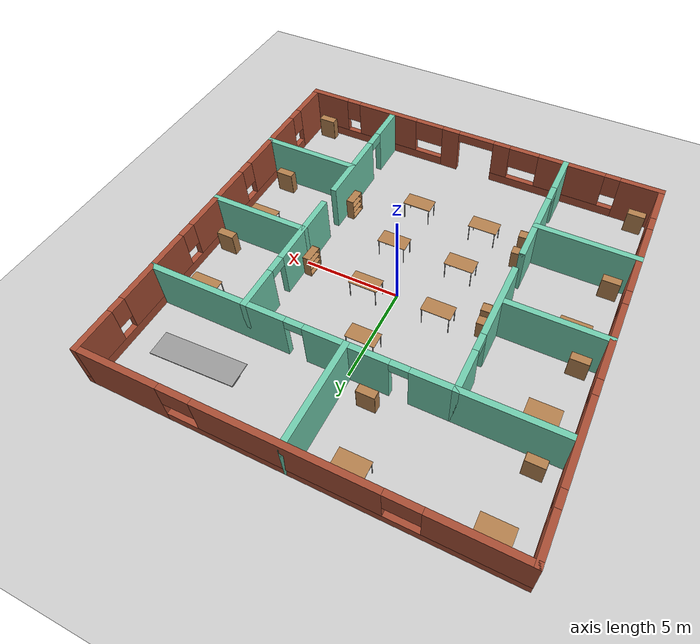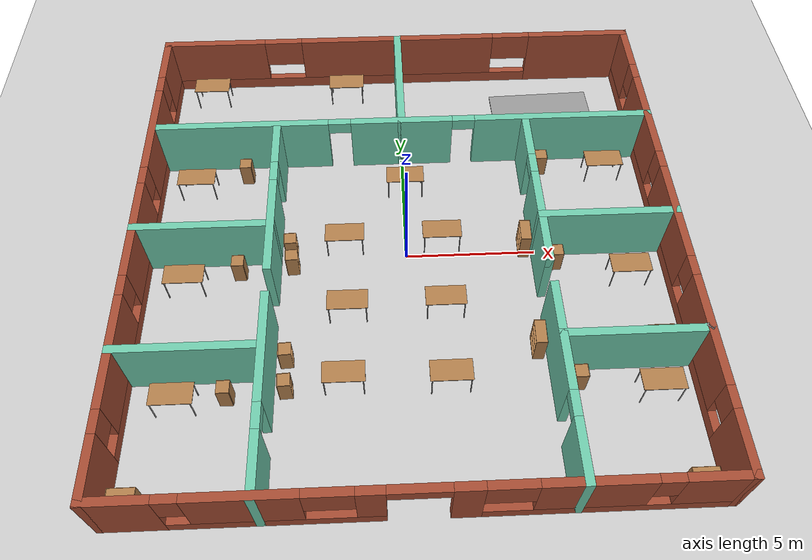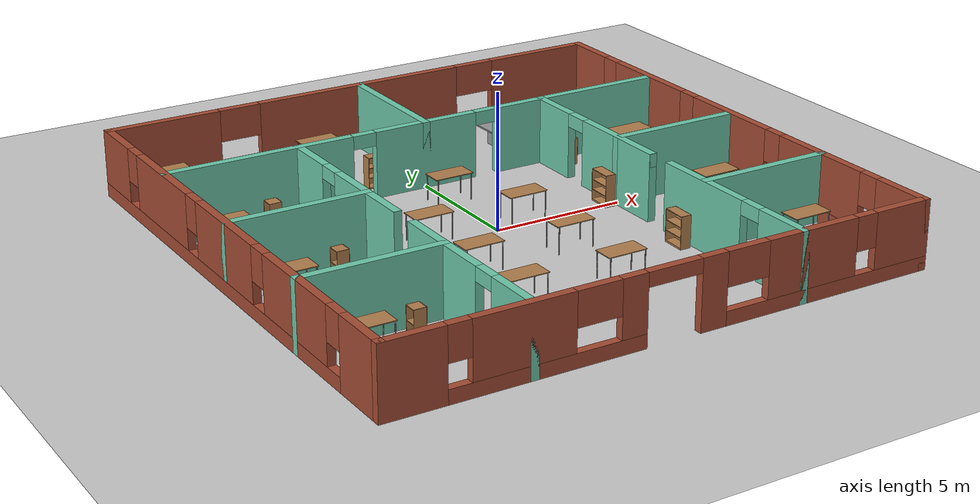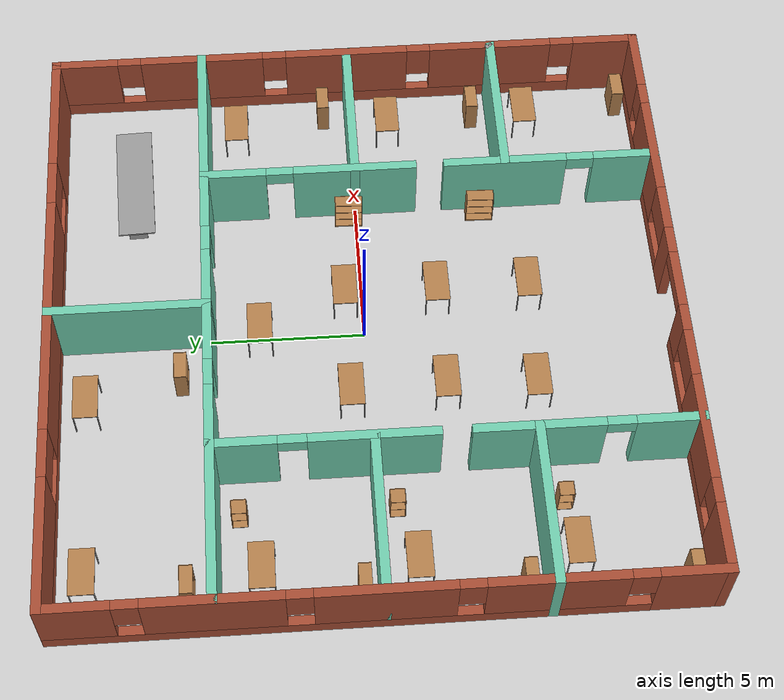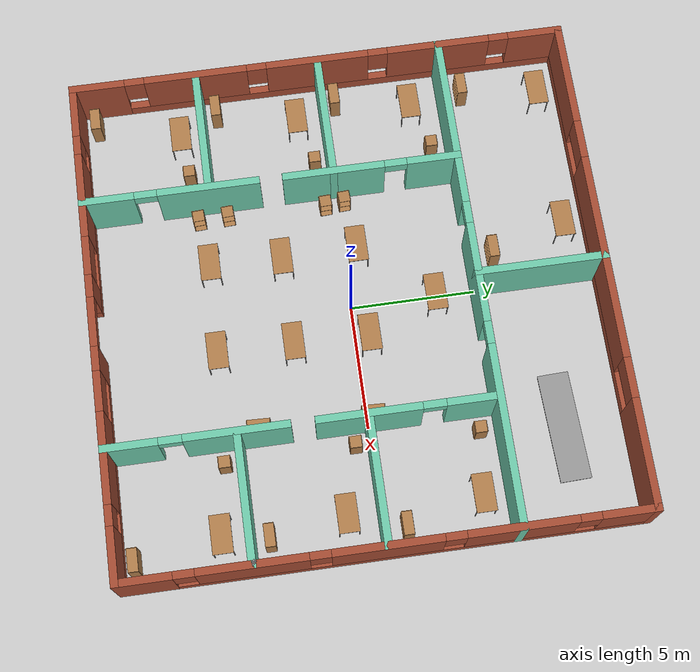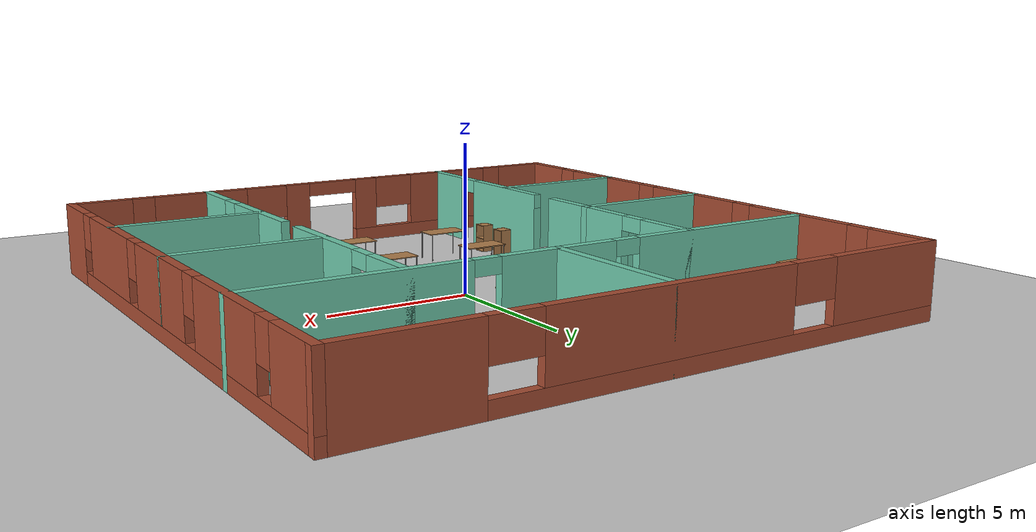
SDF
<sdf version="1.7">
 <world name="default">
  <plugin name="hello" filename="libhello.so"/>
  <light name="sun" type="directional">
   <pose>0 0 10 0 -0 0</pose>
   <diffuse>0.8 0.8 0.8 1</diffuse>
   <specular>0.2 0.2 0.2 1</specular>
   <attenuation>
    <range>1000</range>
    <constant>0.9</constant>
    <linear>0.01</linear>
    <quadratic>0.001</quadratic>
   </attenuation>
   <direction>-0.5 0.1 -0.9</direction>
   <spot><inner_angle>0</inner_angle><outer_angle>0</outer_angle><falloff>0</falloff></spot>
  </light>
  <model name="ground_plane">
   <static>1</static>
   <link name="link">
    <collision name="collision">
     <geometry><plane><normal>0 0 1</normal><size>100 100</size></plane></geometry>
     <surface>
      <contact><collide_bitmask>65535</collide_bitmask></contact>
      <friction><ode><mu>100</mu><mu2>50</mu2></ode></friction>
     </surface>
    </collision>
    <visual name="visual">
     <cast_shadows>0</cast_shadows>
     <geometry><plane><normal>0 0 1</normal><size>100 100</size></plane></geometry>
     <material>
      <script><uri>file://media/materials/scripts/gazebo.material</uri><name>Gazebo/Grey</name></script>
     </material>
    </visual>
   </link>
  </model>
  <gravity>0 0 -9.8</gravity>
  <magnetic_field>6e-06 2.3e-05 -4.2e-05</magnetic_field>
  <atmosphere type="adiabatic"/>
  <physics name="default_physics" default="0" type="ode">
   <max_step_size>0.001</max_step_size>
   <real_time_factor>1</real_time_factor>
   <real_time_update_rate>1000</real_time_update_rate>
  </physics>
  <scene><ambient>0.4 0.4 0.4 1</ambient><background>0.7 0.7 0.7 1</background><shadows>1</shadows></scene>
  <spherical_coordinates>
   <surface_model>EARTH_WGS84</surface_model>
   <latitude_deg>0</latitude_deg>
   <longitude_deg>0</longitude_deg>
   <elevation>0</elevation>
   <heading_deg>0</heading_deg>
  </spherical_coordinates>
  <model name="Building">
   <link name="Wall_0">
    <pose>0 10 0 0 -0 3.14159</pose>
    <visual name="Wall_0_Visual_0">
     <pose>-7.975 0 1.25 0 -0 0</pose>
     <geometry><box><size>4.35 0.3 2.5</size></box></geometry>
     <material>
      <script><uri>file://media/materials/scripts/gazebo.material</uri><name>Gazebo/Bricks</name></script>
      <ambient>1 1 1 1</ambient>
     </material>
     <meta><layer>0</layer></meta>
    </visual>
    <collision name="Wall_0_Collision_0">
     <geometry><box><size>4.35 0.3 2.5</size></box></geometry>
     <pose>-7.975 0 1.25 0 -0 0</pose>
    </collision>
    <visual name="Wall_0_Visual_1">
     <pose>2.175 0 0.25 0 -0 0</pose>
     <geometry><box><size>15.95 0.3 0.5</size></box></geometry>
     <material>
      <script><uri>file://media/materials/scripts/gazebo.material</uri><name>Gazebo/Bricks</name></script>
      <ambient>1 1 1 1</ambient>
     </material>
     <meta><layer>0</layer></meta>
    </visual>
    <collision name="Wall_0_Collision_1">
     <geometry><box><size>15.95 0.3 0.5</size></box></geometry>
     <pose>2.175 0 0.25 0 -0 0</pose>
    </collision>
    <visual name="Wall_0_Visual_2">
     <pose>0 0 1.5 0 -0 0</pose>
     <geometry><box><size>8.4 0.3 2</size></box></geometry>
     <material>
      <script><uri>file://media/materials/scripts/gazebo.material</uri><name>Gazebo/Bricks</name></script>
      <ambient>1 1 1 1</ambient>
     </material>
     <meta><layer>0</layer></meta>
    </visual>
    <collision name="Wall_0_Collision_2">
     <geometry><box><size>8.4 0.3 2</size></box></geometry>
     <pose>0 0 1.5 0 -0 0</pose>
    </collision>
    <visual name="Wall_0_Visual_3">
     <pose>7.975 0 1.5 0 -0 0</pose>
     <geometry><box><size>4.35 0.3 2</size></box></geometry>
     <material>
      <script><uri>file://media/materials/scripts/gazebo.material</uri><name>Gazebo/Bricks</name></script>
      <ambient>1 1 1 1</ambient>
     </material>
     <meta><layer>0</layer></meta>
    </visual>
    <collision name="Wall_0_Collision_3">
     <geometry><box><size>4.35 0.3 2</size></box></geometry>
     <pose>7.975 0 1.5 0 -0 0</pose>
    </collision>
    <visual name="Wall_0_Visual_4">
     <pose>-5 0 1.9 0 -0 0</pose>
     <geometry><box><size>1.6 0.3 1.2</size></box></geometry>
     <material>
      <script><uri>file://media/materials/scripts/gazebo.material</uri><name>Gazebo/Bricks</name></script>
      <ambient>1 1 1 1</ambient>
     </material>
     <meta><layer>0</layer></meta>
    </visual>
    <collision name="Wall_0_Collision_4">
     <geometry><box><size>1.6 0.3 1.2</size></box></geometry>
     <pose>-5 0 1.9 0 -0 0</pose>
    </collision>
    <visual name="Wall_0_Visual_5">
     <pose>5 0 1.9 0 -0 0</pose>
     <geometry><box><size>1.6 0.3 1.2</size></box></geometry>
     <material>
      <script><uri>file://media/materials/scripts/gazebo.material</uri><name>Gazebo/Bricks</name></script>
      <ambient>1 1 1 1</ambient>
     </material>
     <meta><layer>0</layer></meta>
    </visual>
    <collision name="Wall_0_Collision_5">
     <geometry><box><size>1.6 0.3 1.2</size></box></geometry>
     <pose>5 0 1.9 0 -0 0</pose>
    </collision>
   </link>
   <link name="Wall_12">
    <pose>-5 -2.5 0 0 -0 1.5708</pose>
    <visual name="Wall_12_Visual_0">
     <pose>-6.55 0 1.25 0 -0 0</pose>
     <geometry><box><size>2.2 0.3 2.5</size></box></geometry>
     <material>
      <script><uri>file://media/materials/scripts/gazebo.material</uri><name>Gazebo/Grey</name></script>
      <ambient>0.435294 0.796078 0.67451 1</ambient>
     </material>
     <meta><layer>0</layer></meta>
    </visual>
    <collision name="Wall_12_Collision_0">
     <geometry><box><size>2.2 0.3 2.5</size></box></geometry>
     <pose>-6.55 0 1.25 0 -0 0</pose>
    </collision>
    <visual name="Wall_12_Visual_1">
     <pose>-2.5 0 1.25 0 -0 0</pose>
     <geometry><box><size>4.1 0.3 2.5</size></box></geometry>
     <material>
      <script><uri>file://media/materials/scripts/gazebo.material</uri><name>Gazebo/Grey</name></script>
      <ambient>0.435294 0.796078 0.67451 1</ambient>
     </material>
     <meta><layer>0</layer></meta>
    </visual>
    <collision name="Wall_12_Collision_1">
     <geometry><box><size>4.1 0.3 2.5</size></box></geometry>
     <pose>-2.5 0 1.25 0 -0 0</pose>
    </collision>
    <visual name="Wall_12_Visual_2">
     <pose>2.5 0 1.25 0 -0 0</pose>
     <geometry><box><size>4.1 0.3 2.5</size></box></geometry>
     <material>
      <script><uri>file://media/materials/scripts/gazebo.material</uri><name>Gazebo/Grey</name></script>
      <ambient>0.435294 0.796078 0.67451 1</ambient>
     </material>
     <meta><layer>0</layer></meta>
    </visual>
    <collision name="Wall_12_Collision_2">
     <geometry><box><size>4.1 0.3 2.5</size></box></geometry>
     <pose>2.5 0 1.25 0 -0 0</pose>
    </collision>
    <visual name="Wall_12_Visual_3">
     <pose>6.55 0 1.25 0 -0 0</pose>
     <geometry><box><size>2.2 0.3 2.5</size></box></geometry>
     <material>
      <script><uri>file://media/materials/scripts/gazebo.material</uri><name>Gazebo/Grey</name></script>
      <ambient>0.435294 0.796078 0.67451 1</ambient>
     </material>
     <meta><layer>0</layer></meta>
    </visual>
    <collision name="Wall_12_Collision_3">
     <geometry><box><size>2.2 0.3 2.5</size></box></geometry>
     <pose>6.55 0 1.25 0 -0 0</pose>
    </collision>
    <visual name="Wall_12_Visual_4">
     <pose>-5 0 2.25 0 -0 0</pose>
     <geometry><box><size>0.9 0.3 0.5</size></box></geometry>
     <material>
      <script><uri>file://media/materials/scripts/gazebo.material</uri><name>Gazebo/Grey</name></script>
      <ambient>0.435294 0.796078 0.67451 1</ambient>
     </material>
     <meta><layer>0</layer></meta>
    </visual>
    <collision name="Wall_12_Collision_4">
     <geometry><box><size>0.9 0.3 0.5</size></box></geometry>
     <pose>-5 0 2.25 0 -0 0</pose>
    </collision>
    <visual name="Wall_12_Visual_5">
     <pose>-0.45 0 2.25 0 -0 0</pose>
     <geometry><box><size>0 0.3 0.5</size></box></geometry>
     <material>
      <script><uri>file://media/materials/scripts/gazebo.material</uri><name>Gazebo/Grey</name></script>
      <ambient>0.435294 0.796078 0.67451 1</ambient>
     </material>
     <meta><layer>0</layer></meta>
    </visual>
    <collision name="Wall_12_Collision_5">
     <geometry><box><size>0 0.3 0.5</size></box></geometry>
     <pose>-0.45 0 2.25 0 -0 0</pose>
    </collision>
    <visual name="Wall_12_Visual_6">
     <pose>5 0 2.25 0 -0 0</pose>
     <geometry><box><size>0.9 0.3 0.5</size></box></geometry>
     <material>
      <script><uri>file://media/materials/scripts/gazebo.material</uri><name>Gazebo/Grey</name></script>
      <ambient>0.435294 0.796078 0.67451 1</ambient>
     </material>
     <meta><layer>0</layer></meta>
    </visual>
    <collision name="Wall_12_Collision_6">
     <geometry><box><size>0.9 0.3 0.5</size></box></geometry>
     <pose>5 0 2.25 0 -0 0</pose>
    </collision>
   </link>
   <link name="Wall_14">
    <pose>5 -2.5 0 0 0 -1.5708</pose>
    <visual name="Wall_14_Visual_0">
     <pose>-6.55 0 1.25 0 -0 0</pose>
     <geometry><box><size>2.2 0.3 2.5</size></box></geometry>
     <material>
      <script><uri>file://media/materials/scripts/gazebo.material</uri><name>Gazebo/Grey</name></script>
      <ambient>0.435294 0.796078 0.67451 1</ambient>
     </material>
     <meta><layer>0</layer></meta>
    </visual>
    <collision name="Wall_14_Collision_0">
     <geometry><box><size>2.2 0.3 2.5</size></box></geometry>
     <pose>-6.55 0 1.25 0 -0 0</pose>
    </collision>
    <visual name="Wall_14_Visual_1">
     <pose>-2.5 0 1.25 0 -0 0</pose>
     <geometry><box><size>4.1 0.3 2.5</size></box></geometry>
     <material>
      <script><uri>file://media/materials/scripts/gazebo.material</uri><name>Gazebo/Grey</name></script>
      <ambient>0.435294 0.796078 0.67451 1</ambient>
     </material>
     <meta><layer>0</layer></meta>
    </visual>
    <collision name="Wall_14_Collision_1">
     <geometry><box><size>4.1 0.3 2.5</size></box></geometry>
     <pose>-2.5 0 1.25 0 -0 0</pose>
    </collision>
    <visual name="Wall_14_Visual_2">
     <pose>2.5 0 1.25 0 -0 0</pose>
     <geometry><box><size>4.1 0.3 2.5</size></box></geometry>
     <material>
      <script><uri>file://media/materials/scripts/gazebo.material</uri><name>Gazebo/Grey</name></script>
      <ambient>0.435294 0.796078 0.67451 1</ambient>
     </material>
     <meta><layer>0</layer></meta>
    </visual>
    <collision name="Wall_14_Collision_2">
     <geometry><box><size>4.1 0.3 2.5</size></box></geometry>
     <pose>2.5 0 1.25 0 -0 0</pose>
    </collision>
    <visual name="Wall_14_Visual_3">
     <pose>6.55 0 1.25 0 -0 0</pose>
     <geometry><box><size>2.2 0.3 2.5</size></box></geometry>
     <material>
      <script><uri>file://media/materials/scripts/gazebo.material</uri><name>Gazebo/Grey</name></script>
      <ambient>0.435294 0.796078 0.67451 1</ambient>
     </material>
     <meta><layer>0</layer></meta>
    </visual>
    <collision name="Wall_14_Collision_3">
     <geometry><box><size>2.2 0.3 2.5</size></box></geometry>
     <pose>6.55 0 1.25 0 -0 0</pose>
    </collision>
    <visual name="Wall_14_Visual_4">
     <pose>-5 0 2.25 0 -0 0</pose>
     <geometry><box><size>0.9 0.3 0.5</size></box></geometry>
     <material>
      <script><uri>file://media/materials/scripts/gazebo.material</uri><name>Gazebo/Grey</name></script>
      <ambient>0.435294 0.796078 0.67451 1</ambient>
     </material>
     <meta><layer>0</layer></meta>
    </visual>
    <collision name="Wall_14_Collision_4">
     <geometry><box><size>0.9 0.3 0.5</size></box></geometry>
     <pose>-5 0 2.25 0 -0 0</pose>
    </collision>
    <visual name="Wall_14_Visual_5">
     <pose>-0.45 0 2.25 0 -0 0</pose>
     <geometry><box><size>0 0.3 0.5</size></box></geometry>
     <material>
      <script><uri>file://media/materials/scripts/gazebo.material</uri><name>Gazebo/Grey</name></script>
      <ambient>0.435294 0.796078 0.67451 1</ambient>
     </material>
     <meta><layer>0</layer></meta>
    </visual>
    <collision name="Wall_14_Collision_5">
     <geometry><box><size>0 0.3 0.5</size></box></geometry>
     <pose>-0.45 0 2.25 0 -0 0</pose>
    </collision>
    <visual name="Wall_14_Visual_6">
     <pose>5 0 2.25 0 -0 0</pose>
     <geometry><box><size>0.9 0.3 0.5</size></box></geometry>
     <material>
      <script><uri>file://media/materials/scripts/gazebo.material</uri><name>Gazebo/Grey</name></script>
      <ambient>0.435294 0.796078 0.67451 1</ambient>
     </material>
     <meta><layer>0</layer></meta>
    </visual>
    <collision name="Wall_14_Collision_6">
     <geometry><box><size>0.9 0.3 0.5</size></box></geometry>
     <pose>5 0 2.25 0 -0 0</pose>
    </collision>
   </link>
   <link name="Wall_16">
    <collision name="Wall_16_Collision">
     <geometry><box><size>5.3 0.3 2.5</size></box></geometry>
     <pose>0 0 1.25 0 -0 0</pose>
    </collision>
    <visual name="Wall_16_Visual">
     <pose>0 0 1.25 0 -0 0</pose>
     <geometry><box><size>5.3 0.3 2.5</size></box></geometry>
     <material>
      <script><uri>file://media/materials/scripts/gazebo.material</uri><name>Gazebo/Grey</name></script>
      <ambient>0.435294 0.796078 0.67451 1</ambient>
     </material>
     <meta><layer>0</layer></meta>
    </visual>
    <pose>0 7.5 0 0 -0 1.5708</pose>
   </link>
   <link name="Wall_19">
    <collision name="Wall_19_Collision">
     <geometry><box><size>5.3 0.3 2.5</size></box></geometry>
     <pose>0 0 1.25 0 -0 0</pose>
    </collision>
    <visual name="Wall_19_Visual">
     <pose>0 0 1.25 0 -0 0</pose>
     <geometry><box><size>5.3 0.3 2.5</size></box></geometry>
     <material>
      <script><uri>file://media/materials/scripts/gazebo.material</uri><name>Gazebo/Grey</name></script>
      <ambient>0.435294 0.796078 0.67451 1</ambient>
     </material>
     <meta><layer>0</layer></meta>
    </visual>
    <pose>-7.5 -5 0 0 -0 0</pose>
   </link>
   <link name="Wall_2">
    <pose>0 -10 0 0 -0 0</pose>
    <visual name="Wall_2_Visual_0">
     <pose>-9.025 0 1.25 0 -0 0</pose>
     <geometry><box><size>2.25 0.3 2.5</size></box></geometry>
     <material>
      <script><uri>file://media/materials/scripts/gazebo.material</uri><name>Gazebo/Bricks</name></script>
      <ambient>1 1 1 1</ambient>
     </material>
     <meta><layer>0</layer></meta>
    </visual>
    <collision name="Wall_2_Collision_0">
     <geometry><box><size>2.25 0.3 2.5</size></box></geometry>
     <pose>-9.025 0 1.25 0 -0 0</pose>
    </collision>
    <visual name="Wall_2_Visual_1">
     <pose>1.46321 0 1.25 0 -0 0</pose>
     <geometry><box><size>0.973589 0.3 2.5</size></box></geometry>
     <material>
      <script><uri>file://media/materials/scripts/gazebo.material</uri><name>Gazebo/Bricks</name></script>
      <ambient>1 1 1 1</ambient>
     </material>
     <meta><layer>0</layer></meta>
    </visual>
    <collision name="Wall_2_Collision_1">
     <geometry><box><size>0.973589 0.3 2.5</size></box></geometry>
     <pose>1.46321 0 1.25 0 -0 0</pose>
    </collision>
    <visual name="Wall_2_Visual_2">
     <pose>-4.4618 0 0.25 0 -0 0</pose>
     <geometry><box><size>6.87641 0.3 0.5</size></box></geometry>
     <material>
      <script><uri>file://media/materials/scripts/gazebo.material</uri><name>Gazebo/Bricks</name></script>
      <ambient>1 1 1 1</ambient>
     </material>
     <meta><layer>0</layer></meta>
    </visual>
    <collision name="Wall_2_Collision_2">
     <geometry><box><size>6.87641 0.3 0.5</size></box></geometry>
     <pose>-4.4618 0 0.25 0 -0 0</pose>
    </collision>
    <visual name="Wall_2_Visual_3">
     <pose>6.05 0 0.25 0 -0 0</pose>
     <geometry><box><size>8.2 0.3 0.5</size></box></geometry>
     <material>
      <script><uri>file://media/materials/scripts/gazebo.material</uri><name>Gazebo/Bricks</name></script>
      <ambient>1 1 1 1</ambient>
     </material>
     <meta><layer>0</layer></meta>
    </visual>
    <collision name="Wall_2_Collision_3">
     <geometry><box><size>8.2 0.3 0.5</size></box></geometry>
     <pose>6.05 0 0.25 0 -0 0</pose>
    </collision>
    <visual name="Wall_2_Visual_4">
     <pose>-5.325 0 1.5 0 -0 0</pose>
     <geometry><box><size>3.55 0.3 2</size></box></geometry>
     <material>
      <script><uri>file://media/materials/scripts/gazebo.material</uri><name>Gazebo/Bricks</name></script>
      <ambient>1 1 1 1</ambient>
     </material>
     <meta><layer>0</layer></meta>
    </visual>
    <collision name="Wall_2_Collision_4">
     <geometry><box><size>3.55 0.3 2</size></box></geometry>
     <pose>-5.325 0 1.5 0 -0 0</pose>
    </collision>
    <visual name="Wall_2_Visual_5">
     <pose>-1.4868 0 1.5 0 -0 0</pose>
     <geometry><box><size>0.926411 0.3 2</size></box></geometry>
     <material>
      <script><uri>file://media/materials/scripts/gazebo.material</uri><name>Gazebo/Bricks</name></script>
      <ambient>1 1 1 1</ambient>
     </material>
     <meta><layer>0</layer></meta>
    </visual>
    <collision name="Wall_2_Collision_5">
     <geometry><box><size>0.926411 0.3 2</size></box></geometry>
     <pose>-1.4868 0 1.5 0 -0 0</pose>
    </collision>
    <visual name="Wall_2_Visual_6">
     <pose>-1.4868 0 1.5 0 -0 0</pose>
     <geometry><box><size>0.926411 0.3 2</size></box></geometry>
     <material>
      <script><uri>file://media/materials/scripts/gazebo.material</uri><name>Gazebo/Bricks</name></script>
      <ambient>1 1 1 1</ambient>
     </material>
     <meta><layer>0</layer></meta>
    </visual>
    <collision name="Wall_2_Collision_6">
     <geometry><box><size>0.926411 0.3 2</size></box></geometry>
     <pose>-1.4868 0 1.5 0 -0 0</pose>
    </collision>
    <visual name="Wall_2_Visual_7">
     <pose>5.325 0 1.5 0 -0 0</pose>
     <geometry><box><size>3.55 0.3 2</size></box></geometry>
     <material>
      <script><uri>file://media/materials/scripts/gazebo.material</uri><name>Gazebo/Bricks</name></script>
      <ambient>1 1 1 1</ambient>
     </material>
     <meta><layer>0</layer></meta>
    </visual>
    <collision name="Wall_2_Collision_7">
     <geometry><box><size>3.55 0.3 2</size></box></geometry>
     <pose>5.325 0 1.5 0 -0 0</pose>
    </collision>
    <visual name="Wall_2_Visual_8">
     <pose>9.025 0 1.5 0 -0 0</pose>
     <geometry><box><size>2.25 0.3 2</size></box></geometry>
     <material>
      <script><uri>file://media/materials/scripts/gazebo.material</uri><name>Gazebo/Bricks</name></script>
      <ambient>1 1 1 1</ambient>
     </material>
     <meta><layer>0</layer></meta>
    </visual>
    <collision name="Wall_2_Collision_8">
     <geometry><box><size>2.25 0.3 2</size></box></geometry>
     <pose>9.025 0 1.5 0 -0 0</pose>
    </collision>
    <visual name="Wall_2_Visual_9">
     <pose>-7.5 0 1.9 0 -0 0</pose>
     <geometry><box><size>0.8 0.3 1.2</size></box></geometry>
     <material>
      <script><uri>file://media/materials/scripts/gazebo.material</uri><name>Gazebo/Bricks</name></script>
      <ambient>1 1 1 1</ambient>
     </material>
     <meta><layer>0</layer></meta>
    </visual>
    <collision name="Wall_2_Collision_9">
     <geometry><box><size>0.8 0.3 1.2</size></box></geometry>
     <pose>-7.5 0 1.9 0 -0 0</pose>
    </collision>
    <visual name="Wall_2_Visual_10">
     <pose>2.75 0 1.9 0 -0 0</pose>
     <geometry><box><size>1.6 0.3 1.2</size></box></geometry>
     <material>
      <script><uri>file://media/materials/scripts/gazebo.material</uri><name>Gazebo/Bricks</name></script>
      <ambient>1 1 1 1</ambient>
     </material>
     <meta><layer>0</layer></meta>
    </visual>
    <collision name="Wall_2_Collision_10">
     <geometry><box><size>1.6 0.3 1.2</size></box></geometry>
     <pose>2.75 0 1.9 0 -0 0</pose>
    </collision>
    <visual name="Wall_2_Visual_11">
     <pose>-2.75 0 1.9 0 -0 0</pose>
     <geometry><box><size>1.6 0.3 1.2</size></box></geometry>
     <material>
      <script><uri>file://media/materials/scripts/gazebo.material</uri><name>Gazebo/Bricks</name></script>
      <ambient>1 1 1 1</ambient>
     </material>
     <meta><layer>0</layer></meta>
    </visual>
    <collision name="Wall_2_Collision_11">
     <geometry><box><size>1.6 0.3 1.2</size></box></geometry>
     <pose>-2.75 0 1.9 0 -0 0</pose>
    </collision>
    <visual name="Wall_2_Visual_12">
     <pose>7.5 0 1.9 0 -0 0</pose>
     <geometry><box><size>0.8 0.3 1.2</size></box></geometry>
     <material>
      <script><uri>file://media/materials/scripts/gazebo.material</uri><name>Gazebo/Bricks</name></script>
      <ambient>1 1 1 1</ambient>
     </material>
     <meta><layer>0</layer></meta>
    </visual>
    <collision name="Wall_2_Collision_12">
     <geometry><box><size>0.8 0.3 1.2</size></box></geometry>
     <pose>7.5 0 1.9 0 -0 0</pose>
    </collision>
    <visual name="Wall_2_Visual_13">
     <pose>-0.023589 0 2.25 0 -0 0</pose>
     <geometry><box><size>2 0.3 0.5</size></box></geometry>
     <material>
      <script><uri>file://media/materials/scripts/gazebo.material</uri><name>Gazebo/Bricks</name></script>
      <ambient>1 1 1 1</ambient>
     </material>
     <meta><layer>0</layer></meta>
    </visual>
    <collision name="Wall_2_Collision_13">
     <geometry><box><size>2 0.3 0.5</size></box></geometry>
     <pose>-0.023589 0 2.25 0 -0 0</pose>
    </collision>
    <visual name="Wall_2_Visual_14">
     <pose>-0.023589 0 2.25 0 -0 0</pose>
     <geometry><box><size>2 0.3 0.5</size></box></geometry>
     <material>
      <script><uri>file://media/materials/scripts/gazebo.material</uri><name>Gazebo/Bricks</name></script>
      <ambient>1 1 1 1</ambient>
     </material>
     <meta><layer>0</layer></meta>
    </visual>
    <collision name="Wall_2_Collision_14">
     <geometry><box><size>2 0.3 0.5</size></box></geometry>
     <pose>-0.023589 0 2.25 0 -0 0</pose>
    </collision>
   </link>
   <link name="Wall_21">
    <collision name="Wall_21_Collision">
     <geometry><box><size>5.3 0.3 2.5</size></box></geometry>
     <pose>0 0 1.25 0 -0 0</pose>
    </collision>
    <visual name="Wall_21_Visual">
     <pose>0 0 1.25 0 -0 0</pose>
     <geometry><box><size>5.3 0.3 2.5</size></box></geometry>
     <material>
      <script><uri>file://media/materials/scripts/gazebo.material</uri><name>Gazebo/Grey</name></script>
      <ambient>0.435294 0.796078 0.67451 1</ambient>
     </material>
     <meta><layer>0</layer></meta>
    </visual>
    <pose>7.5 -5 0 0 -0 0</pose>
   </link>
   <link name="Wall_22">
    <collision name="Wall_22_Collision">
     <geometry><box><size>0.268816 0.15 2.5</size></box></geometry>
     <pose>0 0 1.25 0 -0 0</pose>
    </collision>
    <visual name="Wall_22_Visual">
     <pose>0 0 1.25 0 -0 0</pose>
     <geometry><box><size>0.268816 0.15 2.5</size></box></geometry>
     <material>
      <script><uri>file://media/materials/scripts/gazebo.material</uri><name>Gazebo/Grey</name></script>
      <ambient>1 1 1 1</ambient>
     </material>
     <meta><layer>0</layer></meta>
    </visual>
    <pose>9.95756 -4.95843 0 0 -0 2.36663</pose>
   </link>
   <link name="Wall_23">
    <collision name="Wall_23_Collision">
     <geometry><box><size>0.268816 0.15 2.5</size></box></geometry>
     <pose>0 0 1.25 0 -0 0</pose>
    </collision>
    <visual name="Wall_23_Visual">
     <pose>0 0 1.25 0 -0 0</pose>
     <geometry><box><size>0.268816 0.15 2.5</size></box></geometry>
     <material>
      <script><uri>file://media/materials/scripts/gazebo.material</uri><name>Gazebo/Grey</name></script>
      <ambient>1 1 1 1</ambient>
     </material>
     <meta><layer>0</layer></meta>
    </visual>
    <pose>9.95756 -4.95843 0 0 0 -0.77496</pose>
   </link>
   <link name="Wall_25">
    <collision name="Wall_25_Collision">
     <geometry><box><size>5.3 0.3 2.5</size></box></geometry>
     <pose>0 0 1.25 0 -0 0</pose>
    </collision>
    <visual name="Wall_25_Visual">
     <pose>0 0 1.25 0 -0 0</pose>
     <geometry><box><size>5.3 0.3 2.5</size></box></geometry>
     <material>
      <script><uri>file://media/materials/scripts/gazebo.material</uri><name>Gazebo/Grey</name></script>
      <ambient>0.435294 0.796078 0.67451 1</ambient>
     </material>
     <meta><layer>0</layer></meta>
    </visual>
    <pose>-7.5 0 0 0 -0 0</pose>
   </link>
   <link name="Wall_27">
    <collision name="Wall_27_Collision">
     <geometry><box><size>5.3 0.3 2.5</size></box></geometry>
     <pose>0 0 1.25 0 -0 0</pose>
    </collision>
    <visual name="Wall_27_Visual">
     <pose>0 0 1.25 0 -0 0</pose>
     <geometry><box><size>5.3 0.3 2.5</size></box></geometry>
     <material>
      <script><uri>file://media/materials/scripts/gazebo.material</uri><name>Gazebo/Grey</name></script>
      <ambient>0.435294 0.796078 0.67451 1</ambient>
     </material>
     <meta><layer>0</layer></meta>
    </visual>
    <pose>7.5 0 0 0 -0 0</pose>
   </link>
   <link name="Wall_5">
    <pose>-10 0 0 0 -0 1.5708</pose>
    <visual name="Wall_5_Visual_0">
     <pose>-9.025 0 1.25 0 -0 0</pose>
     <geometry><box><size>2.25 0.3 2.5</size></box></geometry>
     <material>
      <script><uri>file://media/materials/scripts/gazebo.material</uri><name>Gazebo/Bricks</name></script>
      <ambient>1 1 1 1</ambient>
     </material>
     <meta><layer>0</layer></meta>
    </visual>
    <collision name="Wall_5_Collision_0">
     <geometry><box><size>2.25 0.3 2.5</size></box></geometry>
     <pose>-9.025 0 1.25 0 -0 0</pose>
    </collision>
    <visual name="Wall_5_Visual_1">
     <pose>1.125 0 0.25 0 -0 0</pose>
     <geometry><box><size>18.05 0.3 0.5</size></box></geometry>
     <material>
      <script><uri>file://media/materials/scripts/gazebo.material</uri><name>Gazebo/Bricks</name></script>
      <ambient>1 1 1 1</ambient>
     </material>
     <meta><layer>0</layer></meta>
    </visual>
    <collision name="Wall_5_Collision_1">
     <geometry><box><size>18.05 0.3 0.5</size></box></geometry>
     <pose>1.125 0 0.25 0 -0 0</pose>
    </collision>
    <visual name="Wall_5_Visual_2">
     <pose>-5 0 1.5 0 -0 0</pose>
     <geometry><box><size>4.2 0.3 2</size></box></geometry>
     <material>
      <script><uri>file://media/materials/scripts/gazebo.material</uri><name>Gazebo/Bricks</name></script>
      <ambient>1 1 1 1</ambient>
     </material>
     <meta><layer>0</layer></meta>
    </visual>
    <collision name="Wall_5_Collision_2">
     <geometry><box><size>4.2 0.3 2</size></box></geometry>
     <pose>-5 0 1.5 0 -0 0</pose>
    </collision>
    <visual name="Wall_5_Visual_3">
     <pose>-0.002642 0 1.5 0 -0 0</pose>
     <geometry><box><size>4.19472 0.3 2</size></box></geometry>
     <material>
      <script><uri>file://media/materials/scripts/gazebo.material</uri><name>Gazebo/Bricks</name></script>
      <ambient>1 1 1 1</ambient>
     </material>
     <meta><layer>0</layer></meta>
    </visual>
    <collision name="Wall_5_Collision_3">
     <geometry><box><size>4.19472 0.3 2</size></box></geometry>
     <pose>-0.002642 0 1.5 0 -0 0</pose>
    </collision>
    <visual name="Wall_5_Visual_4">
     <pose>4.99736 0 1.5 0 -0 0</pose>
     <geometry><box><size>4.20528 0.3 2</size></box></geometry>
     <material>
      <script><uri>file://media/materials/scripts/gazebo.material</uri><name>Gazebo/Bricks</name></script>
      <ambient>1 1 1 1</ambient>
     </material>
     <meta><layer>0</layer></meta>
    </visual>
    <collision name="Wall_5_Collision_4">
     <geometry><box><size>4.20528 0.3 2</size></box></geometry>
     <pose>4.99736 0 1.5 0 -0 0</pose>
    </collision>
    <visual name="Wall_5_Visual_5">
     <pose>9.025 0 1.5 0 -0 0</pose>
     <geometry><box><size>2.25 0.3 2</size></box></geometry>
     <material>
      <script><uri>file://media/materials/scripts/gazebo.material</uri><name>Gazebo/Bricks</name></script>
      <ambient>1 1 1 1</ambient>
     </material>
     <meta><layer>0</layer></meta>
    </visual>
    <collision name="Wall_5_Collision_5">
     <geometry><box><size>2.25 0.3 2</size></box></geometry>
     <pose>9.025 0 1.5 0 -0 0</pose>
    </collision>
    <visual name="Wall_5_Visual_6">
     <pose>-7.5 0 1.9 0 -0 0</pose>
     <geometry><box><size>0.8 0.3 1.2</size></box></geometry>
     <material>
      <script><uri>file://media/materials/scripts/gazebo.material</uri><name>Gazebo/Bricks</name></script>
      <ambient>1 1 1 1</ambient>
     </material>
     <meta><layer>0</layer></meta>
    </visual>
    <collision name="Wall_5_Collision_6">
     <geometry><box><size>0.8 0.3 1.2</size></box></geometry>
     <pose>-7.5 0 1.9 0 -0 0</pose>
    </collision>
    <visual name="Wall_5_Visual_7">
     <pose>-2.5 0 1.9 0 -0 0</pose>
     <geometry><box><size>0.8 0.3 1.2</size></box></geometry>
     <material>
      <script><uri>file://media/materials/scripts/gazebo.material</uri><name>Gazebo/Bricks</name></script>
      <ambient>1 1 1 1</ambient>
     </material>
     <meta><layer>0</layer></meta>
    </visual>
    <collision name="Wall_5_Collision_7">
     <geometry><box><size>0.8 0.3 1.2</size></box></geometry>
     <pose>-2.5 0 1.9 0 -0 0</pose>
    </collision>
    <visual name="Wall_5_Visual_8">
     <pose>2.49471 0 1.9 0 -0 0</pose>
     <geometry><box><size>0.8 0.3 1.2</size></box></geometry>
     <material>
      <script><uri>file://media/materials/scripts/gazebo.material</uri><name>Gazebo/Bricks</name></script>
      <ambient>1 1 1 1</ambient>
     </material>
     <meta><layer>0</layer></meta>
    </visual>
    <collision name="Wall_5_Collision_8">
     <geometry><box><size>0.8 0.3 1.2</size></box></geometry>
     <pose>2.49471 0 1.9 0 -0 0</pose>
    </collision>
    <visual name="Wall_5_Visual_9">
     <pose>7.5 0 1.9 0 -0 0</pose>
     <geometry><box><size>0.8 0.3 1.2</size></box></geometry>
     <material>
      <script><uri>file://media/materials/scripts/gazebo.material</uri><name>Gazebo/Bricks</name></script>
      <ambient>1 1 1 1</ambient>
     </material>
     <meta><layer>0</layer></meta>
    </visual>
    <collision name="Wall_5_Collision_9">
     <geometry><box><size>0.8 0.3 1.2</size></box></geometry>
     <pose>7.5 0 1.9 0 -0 0</pose>
    </collision>
   </link>
   <link name="Wall_7">
    <pose>10 0 0 0 -0 1.5708</pose>
    <visual name="Wall_7_Visual_0">
     <pose>-9.025 0 1.25 0 -0 0</pose>
     <geometry><box><size>2.25 0.3 2.5</size></box></geometry>
     <material>
      <script><uri>file://media/materials/scripts/gazebo.material</uri><name>Gazebo/Bricks</name></script>
      <ambient>1 1 1 1</ambient>
     </material>
     <meta><layer>0</layer></meta>
    </visual>
    <collision name="Wall_7_Collision_0">
     <geometry><box><size>2.25 0.3 2.5</size></box></geometry>
     <pose>-9.025 0 1.25 0 -0 0</pose>
    </collision>
    <visual name="Wall_7_Visual_1">
     <pose>1.125 0 0.25 0 -0 0</pose>
     <geometry><box><size>18.05 0.3 0.5</size></box></geometry>
     <material>
      <script><uri>file://media/materials/scripts/gazebo.material</uri><name>Gazebo/Bricks</name></script>
      <ambient>1 1 1 1</ambient>
     </material>
     <meta><layer>0</layer></meta>
    </visual>
    <collision name="Wall_7_Collision_1">
     <geometry><box><size>18.05 0.3 0.5</size></box></geometry>
     <pose>1.125 0 0.25 0 -0 0</pose>
    </collision>
    <visual name="Wall_7_Visual_2">
     <pose>-5 0 1.5 0 -0 0</pose>
     <geometry><box><size>4.2 0.3 2</size></box></geometry>
     <material>
      <script><uri>file://media/materials/scripts/gazebo.material</uri><name>Gazebo/Bricks</name></script>
      <ambient>1 1 1 1</ambient>
     </material>
     <meta><layer>0</layer></meta>
    </visual>
    <collision name="Wall_7_Collision_2">
     <geometry><box><size>4.2 0.3 2</size></box></geometry>
     <pose>-5 0 1.5 0 -0 0</pose>
    </collision>
    <visual name="Wall_7_Visual_3">
     <pose>0 0 1.5 0 -0 0</pose>
     <geometry><box><size>4.2 0.3 2</size></box></geometry>
     <material>
      <script><uri>file://media/materials/scripts/gazebo.material</uri><name>Gazebo/Bricks</name></script>
      <ambient>1 1 1 1</ambient>
     </material>
     <meta><layer>0</layer></meta>
    </visual>
    <collision name="Wall_7_Collision_3">
     <geometry><box><size>4.2 0.3 2</size></box></geometry>
     <pose>0 0 1.5 0 -0 0</pose>
    </collision>
    <visual name="Wall_7_Visual_4">
     <pose>5 0 1.5 0 -0 0</pose>
     <geometry><box><size>4.2 0.3 2</size></box></geometry>
     <material>
      <script><uri>file://media/materials/scripts/gazebo.material</uri><name>Gazebo/Bricks</name></script>
      <ambient>1 1 1 1</ambient>
     </material>
     <meta><layer>0</layer></meta>
    </visual>
    <collision name="Wall_7_Collision_4">
     <geometry><box><size>4.2 0.3 2</size></box></geometry>
     <pose>5 0 1.5 0 -0 0</pose>
    </collision>
    <visual name="Wall_7_Visual_5">
     <pose>9.025 0 1.5 0 -0 0</pose>
     <geometry><box><size>2.25 0.3 2</size></box></geometry>
     <material>
      <script><uri>file://media/materials/scripts/gazebo.material</uri><name>Gazebo/Bricks</name></script>
      <ambient>1 1 1 1</ambient>
     </material>
     <meta><layer>0</layer></meta>
    </visual>
    <collision name="Wall_7_Collision_5">
     <geometry><box><size>2.25 0.3 2</size></box></geometry>
     <pose>9.025 0 1.5 0 -0 0</pose>
    </collision>
    <visual name="Wall_7_Visual_6">
     <pose>-7.5 0 1.9 0 -0 0</pose>
     <geometry><box><size>0.8 0.3 1.2</size></box></geometry>
     <material>
      <script><uri>file://media/materials/scripts/gazebo.material</uri><name>Gazebo/Bricks</name></script>
      <ambient>1 1 1 1</ambient>
     </material>
     <meta><layer>0</layer></meta>
    </visual>
    <collision name="Wall_7_Collision_6">
     <geometry><box><size>0.8 0.3 1.2</size></box></geometry>
     <pose>-7.5 0 1.9 0 -0 0</pose>
    </collision>
    <visual name="Wall_7_Visual_7">
     <pose>-2.5 0 1.9 0 -0 0</pose>
     <geometry><box><size>0.8 0.3 1.2</size></box></geometry>
     <material>
      <script><uri>file://media/materials/scripts/gazebo.material</uri><name>Gazebo/Bricks</name></script>
      <ambient>1 1 1 1</ambient>
     </material>
     <meta><layer>0</layer></meta>
    </visual>
    <collision name="Wall_7_Collision_7">
     <geometry><box><size>0.8 0.3 1.2</size></box></geometry>
     <pose>-2.5 0 1.9 0 -0 0</pose>
    </collision>
    <visual name="Wall_7_Visual_8">
     <pose>2.5 0 1.9 0 -0 0</pose>
     <geometry><box><size>0.8 0.3 1.2</size></box></geometry>
     <material>
      <script><uri>file://media/materials/scripts/gazebo.material</uri><name>Gazebo/Bricks</name></script>
      <ambient>1 1 1 1</ambient>
     </material>
     <meta><layer>0</layer></meta>
    </visual>
    <collision name="Wall_7_Collision_8">
     <geometry><box><size>0.8 0.3 1.2</size></box></geometry>
     <pose>2.5 0 1.9 0 -0 0</pose>
    </collision>
    <visual name="Wall_7_Visual_9">
     <pose>7.5 0 1.9 0 -0 0</pose>
     <geometry><box><size>0.8 0.3 1.2</size></box></geometry>
     <material>
      <script><uri>file://media/materials/scripts/gazebo.material</uri><name>Gazebo/Bricks</name></script>
      <ambient>1 1 1 1</ambient>
     </material>
     <meta><layer>0</layer></meta>
    </visual>
    <collision name="Wall_7_Collision_9">
     <geometry><box><size>0.8 0.3 1.2</size></box></geometry>
     <pose>7.5 0 1.9 0 -0 0</pose>
    </collision>
   </link>
   <link name="Wall_9">
    <pose>0 5 0 0 -0 0</pose>
    <visual name="Wall_9_Visual_0">
     <pose>-6.55 0 1.25 0 -0 0</pose>
     <geometry><box><size>7.2 0.3 2.5</size></box></geometry>
     <material>
      <script><uri>file://media/materials/scripts/gazebo.material</uri><name>Gazebo/Grey</name></script>
      <ambient>0.435294 0.796078 0.67451 1</ambient>
     </material>
     <meta><layer>0</layer></meta>
    </visual>
    <collision name="Wall_9_Collision_0">
     <geometry><box><size>7.2 0.3 2.5</size></box></geometry>
     <pose>-6.55 0 1.25 0 -0 0</pose>
    </collision>
    <visual name="Wall_9_Visual_1">
     <pose>0 0 1.25 0 -0 0</pose>
     <geometry><box><size>4.1 0.3 2.5</size></box></geometry>
     <material>
      <script><uri>file://media/materials/scripts/gazebo.material</uri><name>Gazebo/Grey</name></script>
      <ambient>0.435294 0.796078 0.67451 1</ambient>
     </material>
     <meta><layer>0</layer></meta>
    </visual>
    <collision name="Wall_9_Collision_1">
     <geometry><box><size>4.1 0.3 2.5</size></box></geometry>
     <pose>0 0 1.25 0 -0 0</pose>
    </collision>
    <visual name="Wall_9_Visual_2">
     <pose>6.55 0 1.25 0 -0 0</pose>
     <geometry><box><size>7.2 0.3 2.5</size></box></geometry>
     <material>
      <script><uri>file://media/materials/scripts/gazebo.material</uri><name>Gazebo/Grey</name></script>
      <ambient>0.435294 0.796078 0.67451 1</ambient>
     </material>
     <meta><layer>0</layer></meta>
    </visual>
    <collision name="Wall_9_Collision_2">
     <geometry><box><size>7.2 0.3 2.5</size></box></geometry>
     <pose>6.55 0 1.25 0 -0 0</pose>
    </collision>
    <visual name="Wall_9_Visual_3">
     <pose>-2.5 0 2.25 0 -0 0</pose>
     <geometry><box><size>0.9 0.3 0.5</size></box></geometry>
     <material>
      <script><uri>file://media/materials/scripts/gazebo.material</uri><name>Gazebo/Grey</name></script>
      <ambient>0.435294 0.796078 0.67451 1</ambient>
     </material>
     <meta><layer>0</layer></meta>
    </visual>
    <collision name="Wall_9_Collision_3">
     <geometry><box><size>0.9 0.3 0.5</size></box></geometry>
     <pose>-2.5 0 2.25 0 -0 0</pose>
    </collision>
    <visual name="Wall_9_Visual_4">
     <pose>2.5 0 2.25 0 -0 0</pose>
     <geometry><box><size>0.9 0.3 0.5</size></box></geometry>
     <material>
      <script><uri>file://media/materials/scripts/gazebo.material</uri><name>Gazebo/Grey</name></script>
      <ambient>0.435294 0.796078 0.67451 1</ambient>
     </material>
     <meta><layer>0</layer></meta>
    </visual>
    <collision name="Wall_9_Collision_4">
     <geometry><box><size>0.9 0.3 0.5</size></box></geometry>
     <pose>2.5 0 2.25 0 -0 0</pose>
    </collision>
   </link>
   <static>1</static>
  </model>
  <model name="table">
   <static>1</static>
   <link name="link">
    <collision name="surface">
     <pose>0 0 1 0 -0 0</pose>
     <geometry><box><size>1.5 0.8 0.03</size></box></geometry>
     <surface><friction><ode><mu>0.6</mu><mu2>0.6</mu2></ode></friction></surface>
    </collision>
    <visual name="visual1">
     <pose>0 0 1 0 -0 0</pose>
     <geometry><box><size>1.5 0.8 0.03</size></box></geometry>
     <material>
      <script><uri>file://media/materials/scripts/gazebo.material</uri><name>Gazebo/Wood</name></script>
     </material>
    </visual>
    <collision name="front_left_leg">
     <pose>0.68 0.38 0.5 0 -0 0</pose>
     <geometry><cylinder><radius>0.02</radius><length>1</length></cylinder></geometry>
    </collision>
    <visual name="front_left_leg">
     <pose>0.68 0.38 0.5 0 -0 0</pose>
     <geometry><cylinder><radius>0.02</radius><length>1</length></cylinder></geometry>
     <material>
      <script><uri>file://media/materials/scripts/gazebo.material</uri><name>Gazebo/Grey</name></script>
     </material>
    </visual>
    <collision name="front_right_leg">
     <pose>0.68 -0.38 0.5 0 -0 0</pose>
     <geometry><cylinder><radius>0.02</radius><length>1</length></cylinder></geometry>
    </collision>
    <visual name="front_right_leg">
     <pose>0.68 -0.38 0.5 0 -0 0</pose>
     <geometry><cylinder><radius>0.02</radius><length>1</length></cylinder></geometry>
     <material>
      <script><uri>file://media/materials/scripts/gazebo.material</uri><name>Gazebo/Grey</name></script>
     </material>
    </visual>
    <collision name="back_right_leg">
     <pose>-0.68 -0.38 0.5 0 -0 0</pose>
     <geometry><cylinder><radius>0.02</radius><length>1</length></cylinder></geometry>
    </collision>
    <visual name="back_right_leg">
     <pose>-0.68 -0.38 0.5 0 -0 0</pose>
     <geometry><cylinder><radius>0.02</radius><length>1</length></cylinder></geometry>
     <material>
      <script><uri>file://media/materials/scripts/gazebo.material</uri><name>Gazebo/Grey</name></script>
     </material>
    </visual>
    <collision name="back_left_leg">
     <pose>-0.68 0.38 0.5 0 -0 0</pose>
     <geometry><cylinder><radius>0.02</radius><length>1</length></cylinder></geometry>
    </collision>
    <visual name="back_left_leg">
     <pose>-0.68 0.38 0.5 0 -0 0</pose>
     <geometry><cylinder><radius>0.02</radius><length>1</length></cylinder></geometry>
     <material>
      <script><uri>file://media/materials/scripts/gazebo.material</uri><name>Gazebo/Grey</name></script>
     </material>
    </visual>
   </link>
   <pose>-8.16897 -5.95032 0 0 -0 0</pose>
  </model>
  <model name="table_0">
   <static>1</static>
   <link name="link">
    <collision name="surface">
     <pose>0 0 1 0 -0 0</pose>
     <geometry><box><size>1.5 0.8 0.03</size></box></geometry>
     <surface><friction><ode><mu>0.6</mu><mu2>0.6</mu2></ode></friction></surface>
    </collision>
    <visual name="visual1">
     <pose>0 0 1 0 -0 0</pose>
     <geometry><box><size>1.5 0.8 0.03</size></box></geometry>
     <material>
      <script><uri>file://media/materials/scripts/gazebo.material</uri><name>Gazebo/Wood</name></script>
     </material>
    </visual>
    <collision name="front_left_leg">
     <pose>0.68 0.38 0.5 0 -0 0</pose>
     <geometry><cylinder><radius>0.02</radius><length>1</length></cylinder></geometry>
    </collision>
    <visual name="front_left_leg">
     <pose>0.68 0.38 0.5 0 -0 0</pose>
     <geometry><cylinder><radius>0.02</radius><length>1</length></cylinder></geometry>
     <material>
      <script><uri>file://media/materials/scripts/gazebo.material</uri><name>Gazebo/Grey</name></script>
     </material>
    </visual>
    <collision name="front_right_leg">
     <pose>0.68 -0.38 0.5 0 -0 0</pose>
     <geometry><cylinder><radius>0.02</radius><length>1</length></cylinder></geometry>
    </collision>
    <visual name="front_right_leg">
     <pose>0.68 -0.38 0.5 0 -0 0</pose>
     <geometry><cylinder><radius>0.02</radius><length>1</length></cylinder></geometry>
     <material>
      <script><uri>file://media/materials/scripts/gazebo.material</uri><name>Gazebo/Grey</name></script>
     </material>
    </visual>
    <collision name="back_right_leg">
     <pose>-0.68 -0.38 0.5 0 -0 0</pose>
     <geometry><cylinder><radius>0.02</radius><length>1</length></cylinder></geometry>
    </collision>
    <visual name="back_right_leg">
     <pose>-0.68 -0.38 0.5 0 -0 0</pose>
     <geometry><cylinder><radius>0.02</radius><length>1</length></cylinder></geometry>
     <material>
      <script><uri>file://media/materials/scripts/gazebo.material</uri><name>Gazebo/Grey</name></script>
     </material>
    </visual>
    <collision name="back_left_leg">
     <pose>-0.68 0.38 0.5 0 -0 0</pose>
     <geometry><cylinder><radius>0.02</radius><length>1</length></cylinder></geometry>
    </collision>
    <visual name="back_left_leg">
     <pose>-0.68 0.38 0.5 0 -0 0</pose>
     <geometry><cylinder><radius>0.02</radius><length>1</length></cylinder></geometry>
     <material>
      <script><uri>file://media/materials/scripts/gazebo.material</uri><name>Gazebo/Grey</name></script>
     </material>
    </visual>
   </link>
   <pose>-8.33103 -1.12506 0 0 -0 0</pose>
  </model>
  <model name="table_1">
   <static>1</static>
   <link name="link">
    <collision name="surface">
     <pose>0 0 1 0 -0 0</pose>
     <geometry><box><size>1.5 0.8 0.03</size></box></geometry>
     <surface><friction><ode><mu>0.6</mu><mu2>0.6</mu2></ode></friction></surface>
    </collision>
    <visual name="visual1">
     <pose>0 0 1 0 -0 0</pose>
     <geometry><box><size>1.5 0.8 0.03</size></box></geometry>
     <material>
      <script><uri>file://media/materials/scripts/gazebo.material</uri><name>Gazebo/Wood</name></script>
     </material>
    </visual>
    <collision name="front_left_leg">
     <pose>0.68 0.38 0.5 0 -0 0</pose>
     <geometry><cylinder><radius>0.02</radius><length>1</length></cylinder></geometry>
    </collision>
    <visual name="front_left_leg">
     <pose>0.68 0.38 0.5 0 -0 0</pose>
     <geometry><cylinder><radius>0.02</radius><length>1</length></cylinder></geometry>
     <material>
      <script><uri>file://media/materials/scripts/gazebo.material</uri><name>Gazebo/Grey</name></script>
     </material>
    </visual>
    <collision name="front_right_leg">
     <pose>0.68 -0.38 0.5 0 -0 0</pose>
     <geometry><cylinder><radius>0.02</radius><length>1</length></cylinder></geometry>
    </collision>
    <visual name="front_right_leg">
     <pose>0.68 -0.38 0.5 0 -0 0</pose>
     <geometry><cylinder><radius>0.02</radius><length>1</length></cylinder></geometry>
     <material>
      <script><uri>file://media/materials/scripts/gazebo.material</uri><name>Gazebo/Grey</name></script>
     </material>
    </visual>
    <collision name="back_right_leg">
     <pose>-0.68 -0.38 0.5 0 -0 0</pose>
     <geometry><cylinder><radius>0.02</radius><length>1</length></cylinder></geometry>
    </collision>
    <visual name="back_right_leg">
     <pose>-0.68 -0.38 0.5 0 -0 0</pose>
     <geometry><cylinder><radius>0.02</radius><length>1</length></cylinder></geometry>
     <material>
      <script><uri>file://media/materials/scripts/gazebo.material</uri><name>Gazebo/Grey</name></script>
     </material>
    </visual>
    <collision name="back_left_leg">
     <pose>-0.68 0.38 0.5 0 -0 0</pose>
     <geometry><cylinder><radius>0.02</radius><length>1</length></cylinder></geometry>
    </collision>
    <visual name="back_left_leg">
     <pose>-0.68 0.38 0.5 0 -0 0</pose>
     <geometry><cylinder><radius>0.02</radius><length>1</length></cylinder></geometry>
     <material>
      <script><uri>file://media/materials/scripts/gazebo.material</uri><name>Gazebo/Grey</name></script>
     </material>
    </visual>
   </link>
   <pose>-8.37192 3.60033 0 0 -0 0</pose>
  </model>
  <model name="table_2">
   <static>1</static>
   <link name="link">
    <collision name="surface">
     <pose>0 0 1 0 -0 0</pose>
     <geometry><box><size>1.5 0.8 0.03</size></box></geometry>
     <surface><friction><ode><mu>0.6</mu><mu2>0.6</mu2></ode></friction></surface>
    </collision>
    <visual name="visual1">
     <pose>0 0 1 0 -0 0</pose>
     <geometry><box><size>1.5 0.8 0.03</size></box></geometry>
     <material>
      <script><uri>file://media/materials/scripts/gazebo.material</uri><name>Gazebo/Wood</name></script>
     </material>
    </visual>
    <collision name="front_left_leg">
     <pose>0.68 0.38 0.5 0 -0 0</pose>
     <geometry><cylinder><radius>0.02</radius><length>1</length></cylinder></geometry>
    </collision>
    <visual name="front_left_leg">
     <pose>0.68 0.38 0.5 0 -0 0</pose>
     <geometry><cylinder><radius>0.02</radius><length>1</length></cylinder></geometry>
     <material>
      <script><uri>file://media/materials/scripts/gazebo.material</uri><name>Gazebo/Grey</name></script>
     </material>
    </visual>
    <collision name="front_right_leg">
     <pose>0.68 -0.38 0.5 0 -0 0</pose>
     <geometry><cylinder><radius>0.02</radius><length>1</length></cylinder></geometry>
    </collision>
    <visual name="front_right_leg">
     <pose>0.68 -0.38 0.5 0 -0 0</pose>
     <geometry><cylinder><radius>0.02</radius><length>1</length></cylinder></geometry>
     <material>
      <script><uri>file://media/materials/scripts/gazebo.material</uri><name>Gazebo/Grey</name></script>
     </material>
    </visual>
    <collision name="back_right_leg">
     <pose>-0.68 -0.38 0.5 0 -0 0</pose>
     <geometry><cylinder><radius>0.02</radius><length>1</length></cylinder></geometry>
    </collision>
    <visual name="back_right_leg">
     <pose>-0.68 -0.38 0.5 0 -0 0</pose>
     <geometry><cylinder><radius>0.02</radius><length>1</length></cylinder></geometry>
     <material>
      <script><uri>file://media/materials/scripts/gazebo.material</uri><name>Gazebo/Grey</name></script>
     </material>
    </visual>
    <collision name="back_left_leg">
     <pose>-0.68 0.38 0.5 0 -0 0</pose>
     <geometry><cylinder><radius>0.02</radius><length>1</length></cylinder></geometry>
    </collision>
    <visual name="back_left_leg">
     <pose>-0.68 0.38 0.5 0 -0 0</pose>
     <geometry><cylinder><radius>0.02</radius><length>1</length></cylinder></geometry>
     <material>
      <script><uri>file://media/materials/scripts/gazebo.material</uri><name>Gazebo/Grey</name></script>
     </material>
    </visual>
   </link>
   <pose>8.28999 3.93907 0 0 -0 0</pose>
  </model>
  <model name="table_3">
   <static>1</static>
   <link name="link">
    <collision name="surface">
     <pose>0 0 1 0 -0 0</pose>
     <geometry><box><size>1.5 0.8 0.03</size></box></geometry>
     <surface><friction><ode><mu>0.6</mu><mu2>0.6</mu2></ode></friction></surface>
    </collision>
    <visual name="visual1">
     <pose>0 0 1 0 -0 0</pose>
     <geometry><box><size>1.5 0.8 0.03</size></box></geometry>
     <material>
      <script><uri>file://media/materials/scripts/gazebo.material</uri><name>Gazebo/Wood</name></script>
     </material>
    </visual>
    <collision name="front_left_leg">
     <pose>0.68 0.38 0.5 0 -0 0</pose>
     <geometry><cylinder><radius>0.02</radius><length>1</length></cylinder></geometry>
    </collision>
    <visual name="front_left_leg">
     <pose>0.68 0.38 0.5 0 -0 0</pose>
     <geometry><cylinder><radius>0.02</radius><length>1</length></cylinder></geometry>
     <material>
      <script><uri>file://media/materials/scripts/gazebo.material</uri><name>Gazebo/Grey</name></script>
     </material>
    </visual>
    <collision name="front_right_leg">
     <pose>0.68 -0.38 0.5 0 -0 0</pose>
     <geometry><cylinder><radius>0.02</radius><length>1</length></cylinder></geometry>
    </collision>
    <visual name="front_right_leg">
     <pose>0.68 -0.38 0.5 0 -0 0</pose>
     <geometry><cylinder><radius>0.02</radius><length>1</length></cylinder></geometry>
     <material>
      <script><uri>file://media/materials/scripts/gazebo.material</uri><name>Gazebo/Grey</name></script>
     </material>
    </visual>
    <collision name="back_right_leg">
     <pose>-0.68 -0.38 0.5 0 -0 0</pose>
     <geometry><cylinder><radius>0.02</radius><length>1</length></cylinder></geometry>
    </collision>
    <visual name="back_right_leg">
     <pose>-0.68 -0.38 0.5 0 -0 0</pose>
     <geometry><cylinder><radius>0.02</radius><length>1</length></cylinder></geometry>
     <material>
      <script><uri>file://media/materials/scripts/gazebo.material</uri><name>Gazebo/Grey</name></script>
     </material>
    </visual>
    <collision name="back_left_leg">
     <pose>-0.68 0.38 0.5 0 -0 0</pose>
     <geometry><cylinder><radius>0.02</radius><length>1</length></cylinder></geometry>
    </collision>
    <visual name="back_left_leg">
     <pose>-0.68 0.38 0.5 0 -0 0</pose>
     <geometry><cylinder><radius>0.02</radius><length>1</length></cylinder></geometry>
     <material>
      <script><uri>file://media/materials/scripts/gazebo.material</uri><name>Gazebo/Grey</name></script>
     </material>
    </visual>
   </link>
   <pose>8.35471 -1.29548 0 0 -0 0</pose>
  </model>
  <model name="table_4">
   <static>1</static>
   <link name="link">
    <collision name="surface">
     <pose>0 0 1 0 -0 0</pose>
     <geometry><box><size>1.5 0.8 0.03</size></box></geometry>
     <surface><friction><ode><mu>0.6</mu><mu2>0.6</mu2></ode></friction></surface>
    </collision>
    <visual name="visual1">
     <pose>0 0 1 0 -0 0</pose>
     <geometry><box><size>1.5 0.8 0.03</size></box></geometry>
     <material>
      <script><uri>file://media/materials/scripts/gazebo.material</uri><name>Gazebo/Wood</name></script>
     </material>
    </visual>
    <collision name="front_left_leg">
     <pose>0.68 0.38 0.5 0 -0 0</pose>
     <geometry><cylinder><radius>0.02</radius><length>1</length></cylinder></geometry>
    </collision>
    <visual name="front_left_leg">
     <pose>0.68 0.38 0.5 0 -0 0</pose>
     <geometry><cylinder><radius>0.02</radius><length>1</length></cylinder></geometry>
     <material>
      <script><uri>file://media/materials/scripts/gazebo.material</uri><name>Gazebo/Grey</name></script>
     </material>
    </visual>
    <collision name="front_right_leg">
     <pose>0.68 -0.38 0.5 0 -0 0</pose>
     <geometry><cylinder><radius>0.02</radius><length>1</length></cylinder></geometry>
    </collision>
    <visual name="front_right_leg">
     <pose>0.68 -0.38 0.5 0 -0 0</pose>
     <geometry><cylinder><radius>0.02</radius><length>1</length></cylinder></geometry>
     <material>
      <script><uri>file://media/materials/scripts/gazebo.material</uri><name>Gazebo/Grey</name></script>
     </material>
    </visual>
    <collision name="back_right_leg">
     <pose>-0.68 -0.38 0.5 0 -0 0</pose>
     <geometry><cylinder><radius>0.02</radius><length>1</length></cylinder></geometry>
    </collision>
    <visual name="back_right_leg">
     <pose>-0.68 -0.38 0.5 0 -0 0</pose>
     <geometry><cylinder><radius>0.02</radius><length>1</length></cylinder></geometry>
     <material>
      <script><uri>file://media/materials/scripts/gazebo.material</uri><name>Gazebo/Grey</name></script>
     </material>
    </visual>
    <collision name="back_left_leg">
     <pose>-0.68 0.38 0.5 0 -0 0</pose>
     <geometry><cylinder><radius>0.02</radius><length>1</length></cylinder></geometry>
    </collision>
    <visual name="back_left_leg">
     <pose>-0.68 0.38 0.5 0 -0 0</pose>
     <geometry><cylinder><radius>0.02</radius><length>1</length></cylinder></geometry>
     <material>
      <script><uri>file://media/materials/scripts/gazebo.material</uri><name>Gazebo/Grey</name></script>
     </material>
    </visual>
   </link>
   <pose>8.486 -6.08893 0 0 -0 0</pose>
  </model>
  <model name="table_5">
   <static>1</static>
   <link name="link">
    <collision name="surface">
     <pose>0 0 1 0 -0 0</pose>
     <geometry><box><size>1.5 0.8 0.03</size></box></geometry>
     <surface><friction><ode><mu>0.6</mu><mu2>0.6</mu2></ode></friction></surface>
    </collision>
    <visual name="visual1">
     <pose>0 0 1 0 -0 0</pose>
     <geometry><box><size>1.5 0.8 0.03</size></box></geometry>
     <material>
      <script><uri>file://media/materials/scripts/gazebo.material</uri><name>Gazebo/Wood</name></script>
     </material>
    </visual>
    <collision name="front_left_leg">
     <pose>0.68 0.38 0.5 0 -0 0</pose>
     <geometry><cylinder><radius>0.02</radius><length>1</length></cylinder></geometry>
    </collision>
    <visual name="front_left_leg">
     <pose>0.68 0.38 0.5 0 -0 0</pose>
     <geometry><cylinder><radius>0.02</radius><length>1</length></cylinder></geometry>
     <material>
      <script><uri>file://media/materials/scripts/gazebo.material</uri><name>Gazebo/Grey</name></script>
     </material>
    </visual>
    <collision name="front_right_leg">
     <pose>0.68 -0.38 0.5 0 -0 0</pose>
     <geometry><cylinder><radius>0.02</radius><length>1</length></cylinder></geometry>
    </collision>
    <visual name="front_right_leg">
     <pose>0.68 -0.38 0.5 0 -0 0</pose>
     <geometry><cylinder><radius>0.02</radius><length>1</length></cylinder></geometry>
     <material>
      <script><uri>file://media/materials/scripts/gazebo.material</uri><name>Gazebo/Grey</name></script>
     </material>
    </visual>
    <collision name="back_right_leg">
     <pose>-0.68 -0.38 0.5 0 -0 0</pose>
     <geometry><cylinder><radius>0.02</radius><length>1</length></cylinder></geometry>
    </collision>
    <visual name="back_right_leg">
     <pose>-0.68 -0.38 0.5 0 -0 0</pose>
     <geometry><cylinder><radius>0.02</radius><length>1</length></cylinder></geometry>
     <material>
      <script><uri>file://media/materials/scripts/gazebo.material</uri><name>Gazebo/Grey</name></script>
     </material>
    </visual>
    <collision name="back_left_leg">
     <pose>-0.68 0.38 0.5 0 -0 0</pose>
     <geometry><cylinder><radius>0.02</radius><length>1</length></cylinder></geometry>
    </collision>
    <visual name="back_left_leg">
     <pose>-0.68 0.38 0.5 0 -0 0</pose>
     <geometry><cylinder><radius>0.02</radius><length>1</length></cylinder></geometry>
     <material>
      <script><uri>file://media/materials/scripts/gazebo.material</uri><name>Gazebo/Grey</name></script>
     </material>
    </visual>
   </link>
   <pose>-8.26232 8.95233 0 0 -0 0</pose>
  </model>
  <model name="table_6">
   <static>1</static>
   <link name="link">
    <collision name="surface">
     <pose>0 0 1 0 -0 0</pose>
     <geometry><box><size>1.5 0.8 0.03</size></box></geometry>
     <surface><friction><ode><mu>0.6</mu><mu2>0.6</mu2></ode></friction></surface>
    </collision>
    <visual name="visual1">
     <pose>0 0 1 0 -0 0</pose>
     <geometry><box><size>1.5 0.8 0.03</size></box></geometry>
     <material>
      <script><uri>file://media/materials/scripts/gazebo.material</uri><name>Gazebo/Wood</name></script>
     </material>
    </visual>
    <collision name="front_left_leg">
     <pose>0.68 0.38 0.5 0 -0 0</pose>
     <geometry><cylinder><radius>0.02</radius><length>1</length></cylinder></geometry>
    </collision>
    <visual name="front_left_leg">
     <pose>0.68 0.38 0.5 0 -0 0</pose>
     <geometry><cylinder><radius>0.02</radius><length>1</length></cylinder></geometry>
     <material>
      <script><uri>file://media/materials/scripts/gazebo.material</uri><name>Gazebo/Grey</name></script>
     </material>
    </visual>
    <collision name="front_right_leg">
     <pose>0.68 -0.38 0.5 0 -0 0</pose>
     <geometry><cylinder><radius>0.02</radius><length>1</length></cylinder></geometry>
    </collision>
    <visual name="front_right_leg">
     <pose>0.68 -0.38 0.5 0 -0 0</pose>
     <geometry><cylinder><radius>0.02</radius><length>1</length></cylinder></geometry>
     <material>
      <script><uri>file://media/materials/scripts/gazebo.material</uri><name>Gazebo/Grey</name></script>
     </material>
    </visual>
    <collision name="back_right_leg">
     <pose>-0.68 -0.38 0.5 0 -0 0</pose>
     <geometry><cylinder><radius>0.02</radius><length>1</length></cylinder></geometry>
    </collision>
    <visual name="back_right_leg">
     <pose>-0.68 -0.38 0.5 0 -0 0</pose>
     <geometry><cylinder><radius>0.02</radius><length>1</length></cylinder></geometry>
     <material>
      <script><uri>file://media/materials/scripts/gazebo.material</uri><name>Gazebo/Grey</name></script>
     </material>
    </visual>
    <collision name="back_left_leg">
     <pose>-0.68 0.38 0.5 0 -0 0</pose>
     <geometry><cylinder><radius>0.02</radius><length>1</length></cylinder></geometry>
    </collision>
    <visual name="back_left_leg">
     <pose>-0.68 0.38 0.5 0 -0 0</pose>
     <geometry><cylinder><radius>0.02</radius><length>1</length></cylinder></geometry>
     <material>
      <script><uri>file://media/materials/scripts/gazebo.material</uri><name>Gazebo/Grey</name></script>
     </material>
    </visual>
   </link>
   <pose>-2.31074 8.9588 0 0 -0 0</pose>
  </model>
  <model name="cabinet">
   <static>1</static>
   <link name="cabinet_bottom_plate">
    <inertial>
     <pose>0 0 -1 0 -0 0</pose>
     <inertia><ixx>2.05</ixx><ixy>0</ixy><ixz>0</ixz><iyy>2.05</iyy><iyz>0</iyz><izz>2.05</izz></inertia>
     <mass>25</mass>
    </inertial>
    <collision name="cabinet_bottom_plate_geom">
     <pose>0 0 0.01 0 -0 0</pose>
     <geometry><box><size>0.45 0.45 0.02</size></box></geometry>
    </collision>
    <visual name="cabinet_bottom_plate_geom_visual">
     <pose>0 0 0.01 0 -0 0</pose>
     <geometry><box><size>0.45 0.45 0.02</size></box></geometry>
     <material>
      <script><uri>file://media/materials/scripts/gazebo.material</uri><name>Gazebo/Wood</name></script>
     </material>
    </visual>
    <collision name="cabinet_bottom_plate_geom_cabinet_back_plate">
     <pose>0.235 0 0.51 0 -0 0</pose>
     <geometry><box><size>0.02 0.45 1.02</size></box></geometry>
    </collision>
    <visual name="cabinet_bottom_plate_geom_cabinet_back_plate_visual">
     <pose>0.235 0 0.51 0 -0 0</pose>
     <geometry><box><size>0.02 0.45 1.02</size></box></geometry>
     <material>
      <script><uri>file://media/materials/scripts/gazebo.material</uri><name>Gazebo/Wood</name></script>
     </material>
    </visual>
    <collision name="cabinet_bottom_plate_geom_cabinet_left_plate">
     <pose>0 0.235 0.51 0 -0 0</pose>
     <geometry><box><size>0.45 0.02 1.02</size></box></geometry>
    </collision>
    <visual name="cabinet_bottom_plate_geom_cabinet_left_plate_visual">
     <pose>0 0.235 0.51 0 -0 0</pose>
     <geometry><box><size>0.45 0.02 1.02</size></box></geometry>
     <material>
      <script><uri>file://media/materials/scripts/gazebo.material</uri><name>Gazebo/Wood</name></script>
     </material>
    </visual>
    <collision name="cabinet_bottom_plate_geom_cabinet_middle_plate">
     <pose>0 0 0.51 0 -0 0</pose>
     <geometry><box><size>0.45 0.45 0.02</size></box></geometry>
    </collision>
    <visual name="cabinet_bottom_plate_geom_cabinet_middle_plate_visual">
     <pose>0 0 0.51 0 -0 0</pose>
     <geometry><box><size>0.45 0.45 0.02</size></box></geometry>
     <material>
      <script><uri>file://media/materials/scripts/gazebo.material</uri><name>Gazebo/Wood</name></script>
     </material>
    </visual>
    <collision name="cabinet_bottom_plate_geom_cabinet_right_plate">
     <pose>0 -0.235 0.51 0 -0 0</pose>
     <geometry><box><size>0.45 0.02 1.02</size></box></geometry>
    </collision>
    <visual name="cabinet_bottom_plate_geom_cabinet_right_plate_visual">
     <pose>0 -0.235 0.51 0 -0 0</pose>
     <geometry><box><size>0.45 0.02 1.02</size></box></geometry>
     <material>
      <script><uri>file://media/materials/scripts/gazebo.material</uri><name>Gazebo/Wood</name></script>
     </material>
    </visual>
    <collision name="cabinet_bottom_plate_geom_cabinet_top_plate">
     <pose>0 0 1.01 0 -0 0</pose>
     <geometry><box><size>0.45 0.45 0.02</size></box></geometry>
    </collision>
    <visual name="cabinet_bottom_plate_geom_cabinet_top_plate_visual">
     <pose>0 0 1.01 0 -0 0</pose>
     <geometry><box><size>0.45 0.45 0.02</size></box></geometry>
     <material>
      <script><uri>file://media/materials/scripts/gazebo.material</uri><name>Gazebo/Wood</name></script>
     </material>
    </visual>
   </link>
   <pose>-6.38234 -0.612936 0 0 -0 0</pose>
  </model>
  <model name="cabinet_0">
   <static>1</static>
   <link name="cabinet_bottom_plate">
    <inertial>
     <pose>0 0 -1 0 -0 0</pose>
     <inertia><ixx>2.05</ixx><ixy>0</ixy><ixz>0</ixz><iyy>2.05</iyy><iyz>0</iyz><izz>2.05</izz></inertia>
     <mass>25</mass>
    </inertial>
    <collision name="cabinet_bottom_plate_geom">
     <pose>0 0 0.01 0 -0 0</pose>
     <geometry><box><size>0.45 0.45 0.02</size></box></geometry>
    </collision>
    <visual name="cabinet_bottom_plate_geom_visual">
     <pose>0 0 0.01 0 -0 0</pose>
     <geometry><box><size>0.45 0.45 0.02</size></box></geometry>
     <material>
      <script><uri>file://media/materials/scripts/gazebo.material</uri><name>Gazebo/Wood</name></script>
     </material>
    </visual>
    <collision name="cabinet_bottom_plate_geom_cabinet_back_plate">
     <pose>0.235 0 0.51 0 -0 0</pose>
     <geometry><box><size>0.02 0.45 1.02</size></box></geometry>
    </collision>
    <visual name="cabinet_bottom_plate_geom_cabinet_back_plate_visual">
     <pose>0.235 0 0.51 0 -0 0</pose>
     <geometry><box><size>0.02 0.45 1.02</size></box></geometry>
     <material>
      <script><uri>file://media/materials/scripts/gazebo.material</uri><name>Gazebo/Wood</name></script>
     </material>
    </visual>
    <collision name="cabinet_bottom_plate_geom_cabinet_left_plate">
     <pose>0 0.235 0.51 0 -0 0</pose>
     <geometry><box><size>0.45 0.02 1.02</size></box></geometry>
    </collision>
    <visual name="cabinet_bottom_plate_geom_cabinet_left_plate_visual">
     <pose>0 0.235 0.51 0 -0 0</pose>
     <geometry><box><size>0.45 0.02 1.02</size></box></geometry>
     <material>
      <script><uri>file://media/materials/scripts/gazebo.material</uri><name>Gazebo/Wood</name></script>
     </material>
    </visual>
    <collision name="cabinet_bottom_plate_geom_cabinet_middle_plate">
     <pose>0 0 0.51 0 -0 0</pose>
     <geometry><box><size>0.45 0.45 0.02</size></box></geometry>
    </collision>
    <visual name="cabinet_bottom_plate_geom_cabinet_middle_plate_visual">
     <pose>0 0 0.51 0 -0 0</pose>
     <geometry><box><size>0.45 0.45 0.02</size></box></geometry>
     <material>
      <script><uri>file://media/materials/scripts/gazebo.material</uri><name>Gazebo/Wood</name></script>
     </material>
    </visual>
    <collision name="cabinet_bottom_plate_geom_cabinet_right_plate">
     <pose>0 -0.235 0.51 0 -0 0</pose>
     <geometry><box><size>0.45 0.02 1.02</size></box></geometry>
    </collision>
    <visual name="cabinet_bottom_plate_geom_cabinet_right_plate_visual">
     <pose>0 -0.235 0.51 0 -0 0</pose>
     <geometry><box><size>0.45 0.02 1.02</size></box></geometry>
     <material>
      <script><uri>file://media/materials/scripts/gazebo.material</uri><name>Gazebo/Wood</name></script>
     </material>
    </visual>
    <collision name="cabinet_bottom_plate_geom_cabinet_top_plate">
     <pose>0 0 1.01 0 -0 0</pose>
     <geometry><box><size>0.45 0.45 0.02</size></box></geometry>
    </collision>
    <visual name="cabinet_bottom_plate_geom_cabinet_top_plate_visual">
     <pose>0 0 1.01 0 -0 0</pose>
     <geometry><box><size>0.45 0.45 0.02</size></box></geometry>
     <material>
      <script><uri>file://media/materials/scripts/gazebo.material</uri><name>Gazebo/Wood</name></script>
     </material>
    </visual>
   </link>
   <pose>-6.4417 4.23866 0 0 -0 0</pose>
  </model>
  <model name="cabinet_1">
   <static>1</static>
   <link name="cabinet_bottom_plate">
    <inertial>
     <pose>0 0 -1 0 -0 0</pose>
     <inertia><ixx>2.05</ixx><ixy>0</ixy><ixz>0</ixz><iyy>2.05</iyy><iyz>0</iyz><izz>2.05</izz></inertia>
     <mass>25</mass>
    </inertial>
    <collision name="cabinet_bottom_plate_geom">
     <pose>0 0 0.01 0 -0 0</pose>
     <geometry><box><size>0.45 0.45 0.02</size></box></geometry>
    </collision>
    <visual name="cabinet_bottom_plate_geom_visual">
     <pose>0 0 0.01 0 -0 0</pose>
     <geometry><box><size>0.45 0.45 0.02</size></box></geometry>
     <material>
      <script><uri>file://media/materials/scripts/gazebo.material</uri><name>Gazebo/Wood</name></script>
     </material>
    </visual>
    <collision name="cabinet_bottom_plate_geom_cabinet_back_plate">
     <pose>0.235 0 0.51 0 -0 0</pose>
     <geometry><box><size>0.02 0.45 1.02</size></box></geometry>
    </collision>
    <visual name="cabinet_bottom_plate_geom_cabinet_back_plate_visual">
     <pose>0.235 0 0.51 0 -0 0</pose>
     <geometry><box><size>0.02 0.45 1.02</size></box></geometry>
     <material>
      <script><uri>file://media/materials/scripts/gazebo.material</uri><name>Gazebo/Wood</name></script>
     </material>
    </visual>
    <collision name="cabinet_bottom_plate_geom_cabinet_left_plate">
     <pose>0 0.235 0.51 0 -0 0</pose>
     <geometry><box><size>0.45 0.02 1.02</size></box></geometry>
    </collision>
    <visual name="cabinet_bottom_plate_geom_cabinet_left_plate_visual">
     <pose>0 0.235 0.51 0 -0 0</pose>
     <geometry><box><size>0.45 0.02 1.02</size></box></geometry>
     <material>
      <script><uri>file://media/materials/scripts/gazebo.material</uri><name>Gazebo/Wood</name></script>
     </material>
    </visual>
    <collision name="cabinet_bottom_plate_geom_cabinet_middle_plate">
     <pose>0 0 0.51 0 -0 0</pose>
     <geometry><box><size>0.45 0.45 0.02</size></box></geometry>
    </collision>
    <visual name="cabinet_bottom_plate_geom_cabinet_middle_plate_visual">
     <pose>0 0 0.51 0 -0 0</pose>
     <geometry><box><size>0.45 0.45 0.02</size></box></geometry>
     <material>
      <script><uri>file://media/materials/scripts/gazebo.material</uri><name>Gazebo/Wood</name></script>
     </material>
    </visual>
    <collision name="cabinet_bottom_plate_geom_cabinet_right_plate">
     <pose>0 -0.235 0.51 0 -0 0</pose>
     <geometry><box><size>0.45 0.02 1.02</size></box></geometry>
    </collision>
    <visual name="cabinet_bottom_plate_geom_cabinet_right_plate_visual">
     <pose>0 -0.235 0.51 0 -0 0</pose>
     <geometry><box><size>0.45 0.02 1.02</size></box></geometry>
     <material>
      <script><uri>file://media/materials/scripts/gazebo.material</uri><name>Gazebo/Wood</name></script>
     </material>
    </visual>
    <collision name="cabinet_bottom_plate_geom_cabinet_top_plate">
     <pose>0 0 1.01 0 -0 0</pose>
     <geometry><box><size>0.45 0.45 0.02</size></box></geometry>
    </collision>
    <visual name="cabinet_bottom_plate_geom_cabinet_top_plate_visual">
     <pose>0 0 1.01 0 -0 0</pose>
     <geometry><box><size>0.45 0.45 0.02</size></box></geometry>
     <material>
      <script><uri>file://media/materials/scripts/gazebo.material</uri><name>Gazebo/Wood</name></script>
     </material>
    </visual>
   </link>
   <pose>-6.45913 -5.77414 0 0 -0 0</pose>
  </model>
  <model name="cabinet_2">
   <static>1</static>
   <link name="cabinet_bottom_plate">
    <inertial>
     <pose>0 0 -1 0 -0 0</pose>
     <inertia><ixx>2.05</ixx><ixy>0</ixy><ixz>0</ixz><iyy>2.05</iyy><iyz>0</iyz><izz>2.05</izz></inertia>
     <mass>25</mass>
    </inertial>
    <collision name="cabinet_bottom_plate_geom">
     <pose>0 0 0.01 0 -0 0</pose>
     <geometry><box><size>0.45 0.45 0.02</size></box></geometry>
    </collision>
    <visual name="cabinet_bottom_plate_geom_visual">
     <pose>0 0 0.01 0 -0 0</pose>
     <geometry><box><size>0.45 0.45 0.02</size></box></geometry>
     <material>
      <script><uri>file://media/materials/scripts/gazebo.material</uri><name>Gazebo/Wood</name></script>
     </material>
    </visual>
    <collision name="cabinet_bottom_plate_geom_cabinet_back_plate">
     <pose>0.235 0 0.51 0 -0 0</pose>
     <geometry><box><size>0.02 0.45 1.02</size></box></geometry>
    </collision>
    <visual name="cabinet_bottom_plate_geom_cabinet_back_plate_visual">
     <pose>0.235 0 0.51 0 -0 0</pose>
     <geometry><box><size>0.02 0.45 1.02</size></box></geometry>
     <material>
      <script><uri>file://media/materials/scripts/gazebo.material</uri><name>Gazebo/Wood</name></script>
     </material>
    </visual>
    <collision name="cabinet_bottom_plate_geom_cabinet_left_plate">
     <pose>0 0.235 0.51 0 -0 0</pose>
     <geometry><box><size>0.45 0.02 1.02</size></box></geometry>
    </collision>
    <visual name="cabinet_bottom_plate_geom_cabinet_left_plate_visual">
     <pose>0 0.235 0.51 0 -0 0</pose>
     <geometry><box><size>0.45 0.02 1.02</size></box></geometry>
     <material>
      <script><uri>file://media/materials/scripts/gazebo.material</uri><name>Gazebo/Wood</name></script>
     </material>
    </visual>
    <collision name="cabinet_bottom_plate_geom_cabinet_middle_plate">
     <pose>0 0 0.51 0 -0 0</pose>
     <geometry><box><size>0.45 0.45 0.02</size></box></geometry>
    </collision>
    <visual name="cabinet_bottom_plate_geom_cabinet_middle_plate_visual">
     <pose>0 0 0.51 0 -0 0</pose>
     <geometry><box><size>0.45 0.45 0.02</size></box></geometry>
     <material>
      <script><uri>file://media/materials/scripts/gazebo.material</uri><name>Gazebo/Wood</name></script>
     </material>
    </visual>
    <collision name="cabinet_bottom_plate_geom_cabinet_right_plate">
     <pose>0 -0.235 0.51 0 -0 0</pose>
     <geometry><box><size>0.45 0.02 1.02</size></box></geometry>
    </collision>
    <visual name="cabinet_bottom_plate_geom_cabinet_right_plate_visual">
     <pose>0 -0.235 0.51 0 -0 0</pose>
     <geometry><box><size>0.45 0.02 1.02</size></box></geometry>
     <material>
      <script><uri>file://media/materials/scripts/gazebo.material</uri><name>Gazebo/Wood</name></script>
     </material>
    </visual>
    <collision name="cabinet_bottom_plate_geom_cabinet_top_plate">
     <pose>0 0 1.01 0 -0 0</pose>
     <geometry><box><size>0.45 0.45 0.02</size></box></geometry>
    </collision>
    <visual name="cabinet_bottom_plate_geom_cabinet_top_plate_visual">
     <pose>0 0 1.01 0 -0 0</pose>
     <geometry><box><size>0.45 0.45 0.02</size></box></geometry>
     <material>
      <script><uri>file://media/materials/scripts/gazebo.material</uri><name>Gazebo/Wood</name></script>
     </material>
    </visual>
   </link>
   <pose>5.75063 4.24851 0 0 -0 0</pose>
  </model>
  <model name="cabinet_3">
   <static>1</static>
   <link name="cabinet_bottom_plate">
    <inertial>
     <pose>0 0 -1 0 -0 0</pose>
     <inertia><ixx>2.05</ixx><ixy>0</ixy><ixz>0</ixz><iyy>2.05</iyy><iyz>0</iyz><izz>2.05</izz></inertia>
     <mass>25</mass>
    </inertial>
    <collision name="cabinet_bottom_plate_geom">
     <pose>0 0 0.01 0 -0 0</pose>
     <geometry><box><size>0.45 0.45 0.02</size></box></geometry>
    </collision>
    <visual name="cabinet_bottom_plate_geom_visual">
     <pose>0 0 0.01 0 -0 0</pose>
     <geometry><box><size>0.45 0.45 0.02</size></box></geometry>
     <material>
      <script><uri>file://media/materials/scripts/gazebo.material</uri><name>Gazebo/Wood</name></script>
     </material>
    </visual>
    <collision name="cabinet_bottom_plate_geom_cabinet_back_plate">
     <pose>0.235 0 0.51 0 -0 0</pose>
     <geometry><box><size>0.02 0.45 1.02</size></box></geometry>
    </collision>
    <visual name="cabinet_bottom_plate_geom_cabinet_back_plate_visual">
     <pose>0.235 0 0.51 0 -0 0</pose>
     <geometry><box><size>0.02 0.45 1.02</size></box></geometry>
     <material>
      <script><uri>file://media/materials/scripts/gazebo.material</uri><name>Gazebo/Wood</name></script>
     </material>
    </visual>
    <collision name="cabinet_bottom_plate_geom_cabinet_left_plate">
     <pose>0 0.235 0.51 0 -0 0</pose>
     <geometry><box><size>0.45 0.02 1.02</size></box></geometry>
    </collision>
    <visual name="cabinet_bottom_plate_geom_cabinet_left_plate_visual">
     <pose>0 0.235 0.51 0 -0 0</pose>
     <geometry><box><size>0.45 0.02 1.02</size></box></geometry>
     <material>
      <script><uri>file://media/materials/scripts/gazebo.material</uri><name>Gazebo/Wood</name></script>
     </material>
    </visual>
    <collision name="cabinet_bottom_plate_geom_cabinet_middle_plate">
     <pose>0 0 0.51 0 -0 0</pose>
     <geometry><box><size>0.45 0.45 0.02</size></box></geometry>
    </collision>
    <visual name="cabinet_bottom_plate_geom_cabinet_middle_plate_visual">
     <pose>0 0 0.51 0 -0 0</pose>
     <geometry><box><size>0.45 0.45 0.02</size></box></geometry>
     <material>
      <script><uri>file://media/materials/scripts/gazebo.material</uri><name>Gazebo/Wood</name></script>
     </material>
    </visual>
    <collision name="cabinet_bottom_plate_geom_cabinet_right_plate">
     <pose>0 -0.235 0.51 0 -0 0</pose>
     <geometry><box><size>0.45 0.02 1.02</size></box></geometry>
    </collision>
    <visual name="cabinet_bottom_plate_geom_cabinet_right_plate_visual">
     <pose>0 -0.235 0.51 0 -0 0</pose>
     <geometry><box><size>0.45 0.02 1.02</size></box></geometry>
     <material>
      <script><uri>file://media/materials/scripts/gazebo.material</uri><name>Gazebo/Wood</name></script>
     </material>
    </visual>
    <collision name="cabinet_bottom_plate_geom_cabinet_top_plate">
     <pose>0 0 1.01 0 -0 0</pose>
     <geometry><box><size>0.45 0.45 0.02</size></box></geometry>
    </collision>
    <visual name="cabinet_bottom_plate_geom_cabinet_top_plate_visual">
     <pose>0 0 1.01 0 -0 0</pose>
     <geometry><box><size>0.45 0.45 0.02</size></box></geometry>
     <material>
      <script><uri>file://media/materials/scripts/gazebo.material</uri><name>Gazebo/Wood</name></script>
     </material>
    </visual>
   </link>
   <pose>5.68059 -0.60227 0 0 -0 0</pose>
  </model>
  <model name="cabinet_4">
   <static>1</static>
   <link name="cabinet_bottom_plate">
    <inertial>
     <pose>0 0 -1 0 -0 0</pose>
     <inertia><ixx>2.05</ixx><ixy>0</ixy><ixz>0</ixz><iyy>2.05</iyy><iyz>0</iyz><izz>2.05</izz></inertia>
     <mass>25</mass>
    </inertial>
    <collision name="cabinet_bottom_plate_geom">
     <pose>0 0 0.01 0 -0 0</pose>
     <geometry><box><size>0.45 0.45 0.02</size></box></geometry>
    </collision>
    <visual name="cabinet_bottom_plate_geom_visual">
     <pose>0 0 0.01 0 -0 0</pose>
     <geometry><box><size>0.45 0.45 0.02</size></box></geometry>
     <material>
      <script><uri>file://media/materials/scripts/gazebo.material</uri><name>Gazebo/Wood</name></script>
     </material>
    </visual>
    <collision name="cabinet_bottom_plate_geom_cabinet_back_plate">
     <pose>0.235 0 0.51 0 -0 0</pose>
     <geometry><box><size>0.02 0.45 1.02</size></box></geometry>
    </collision>
    <visual name="cabinet_bottom_plate_geom_cabinet_back_plate_visual">
     <pose>0.235 0 0.51 0 -0 0</pose>
     <geometry><box><size>0.02 0.45 1.02</size></box></geometry>
     <material>
      <script><uri>file://media/materials/scripts/gazebo.material</uri><name>Gazebo/Wood</name></script>
     </material>
    </visual>
    <collision name="cabinet_bottom_plate_geom_cabinet_left_plate">
     <pose>0 0.235 0.51 0 -0 0</pose>
     <geometry><box><size>0.45 0.02 1.02</size></box></geometry>
    </collision>
    <visual name="cabinet_bottom_plate_geom_cabinet_left_plate_visual">
     <pose>0 0.235 0.51 0 -0 0</pose>
     <geometry><box><size>0.45 0.02 1.02</size></box></geometry>
     <material>
      <script><uri>file://media/materials/scripts/gazebo.material</uri><name>Gazebo/Wood</name></script>
     </material>
    </visual>
    <collision name="cabinet_bottom_plate_geom_cabinet_middle_plate">
     <pose>0 0 0.51 0 -0 0</pose>
     <geometry><box><size>0.45 0.45 0.02</size></box></geometry>
    </collision>
    <visual name="cabinet_bottom_plate_geom_cabinet_middle_plate_visual">
     <pose>0 0 0.51 0 -0 0</pose>
     <geometry><box><size>0.45 0.45 0.02</size></box></geometry>
     <material>
      <script><uri>file://media/materials/scripts/gazebo.material</uri><name>Gazebo/Wood</name></script>
     </material>
    </visual>
    <collision name="cabinet_bottom_plate_geom_cabinet_right_plate">
     <pose>0 -0.235 0.51 0 -0 0</pose>
     <geometry><box><size>0.45 0.02 1.02</size></box></geometry>
    </collision>
    <visual name="cabinet_bottom_plate_geom_cabinet_right_plate_visual">
     <pose>0 -0.235 0.51 0 -0 0</pose>
     <geometry><box><size>0.45 0.02 1.02</size></box></geometry>
     <material>
      <script><uri>file://media/materials/scripts/gazebo.material</uri><name>Gazebo/Wood</name></script>
     </material>
    </visual>
    <collision name="cabinet_bottom_plate_geom_cabinet_top_plate">
     <pose>0 0 1.01 0 -0 0</pose>
     <geometry><box><size>0.45 0.45 0.02</size></box></geometry>
    </collision>
    <visual name="cabinet_bottom_plate_geom_cabinet_top_plate_visual">
     <pose>0 0 1.01 0 -0 0</pose>
     <geometry><box><size>0.45 0.45 0.02</size></box></geometry>
     <material>
      <script><uri>file://media/materials/scripts/gazebo.material</uri><name>Gazebo/Wood</name></script>
     </material>
    </visual>
   </link>
   <pose>5.75863 -5.67123 0 0 -0 0</pose>
  </model>
  <model name="bookshelf">
   <static>1</static>
   <link name="link">
    <inertial><mass>1</mass></inertial>
    <collision name="back">
     <pose>0 0.005 0.6 0 -0 0</pose>
     <geometry><box><size>0.9 0.01 1.2</size></box></geometry>
    </collision>
    <visual name="visual1">
     <pose>0 0.005 0.6 0 -0 0</pose>
     <geometry><box><size>0.9 0.01 1.2</size></box></geometry>
     <material>
      <script><uri>file://media/materials/scripts/gazebo.material</uri><name>Gazebo/Wood</name></script>
     </material>
    </visual>
    <collision name="left_side">
     <pose>0.45 -0.195 0.6 0 -0 0</pose>
     <geometry><box><size>0.02 0.4 1.2</size></box></geometry>
    </collision>
    <visual name="visual2">
     <pose>0.45 -0.195 0.6 0 -0 0</pose>
     <geometry><box><size>0.02 0.4 1.2</size></box></geometry>
     <material>
      <script><uri>file://media/materials/scripts/gazebo.material</uri><name>Gazebo/Wood</name></script>
     </material>
    </visual>
    <collision name="right_side">
     <pose>-0.45 -0.195 0.6 0 -0 0</pose>
     <geometry><box><size>0.02 0.4 1.2</size></box></geometry>
    </collision>
    <visual name="visual3">
     <pose>-0.45 -0.195 0.6 0 -0 0</pose>
     <geometry><box><size>0.02 0.4 1.2</size></box></geometry>
     <material>
      <script><uri>file://media/materials/scripts/gazebo.material</uri><name>Gazebo/Wood</name></script>
     </material>
    </visual>
    <collision name="bottom">
     <pose>0 -0.195 0.03 0 -0 0</pose>
     <geometry><box><size>0.88 0.4 0.06</size></box></geometry>
    </collision>
    <visual name="visual4">
     <pose>0 -0.195 0.03 0 -0 0</pose>
     <geometry><box><size>0.88 0.4 0.06</size></box></geometry>
     <material>
      <script><uri>file://media/materials/scripts/gazebo.material</uri><name>Gazebo/Wood</name></script>
     </material>
    </visual>
    <collision name="top">
     <pose>0 -0.195 1.19 0 -0 0</pose>
     <geometry><box><size>0.88 0.4 0.02</size></box></geometry>
    </collision>
    <visual name="visual5">
     <pose>0 -0.195 1.19 0 -0 0</pose>
     <geometry><box><size>0.88 0.4 0.02</size></box></geometry>
     <material>
      <script><uri>file://media/materials/scripts/gazebo.material</uri><name>Gazebo/Wood</name></script>
     </material>
    </visual>
    <collision name="low_shelf">
     <pose>0 -0.195 0.43 0 -0 0</pose>
     <geometry><box><size>0.88 0.4 0.02</size></box></geometry>
    </collision>
    <visual name="visual6">
     <pose>0 -0.195 0.43 0 -0 0</pose>
     <geometry><box><size>0.88 0.4 0.02</size></box></geometry>
     <material>
      <script><uri>file://media/materials/scripts/gazebo.material</uri><name>Gazebo/Wood</name></script>
     </material>
    </visual>
    <collision name="high_shelf">
     <pose>0 -0.195 0.8 0 -0 0</pose>
     <geometry><box><size>0.88 0.4 0.02</size></box></geometry>
    </collision>
    <visual name="visual7">
     <pose>0 -0.195 0.8 0 -0 0</pose>
     <geometry><box><size>0.88 0.4 0.02</size></box></geometry>
     <material>
      <script><uri>file://media/materials/scripts/gazebo.material</uri><name>Gazebo/Wood</name></script>
     </material>
    </visual>
   </link>
   <pose>-9.16992 -4.20554 0 0 -0 0</pose>
  </model>
  <model name="bookshelf_0">
   <static>1</static>
   <link name="link">
    <inertial><mass>1</mass></inertial>
    <collision name="back">
     <pose>0 0.005 0.6 0 -0 0</pose>
     <geometry><box><size>0.9 0.01 1.2</size></box></geometry>
    </collision>
    <visual name="visual1">
     <pose>0 0.005 0.6 0 -0 0</pose>
     <geometry><box><size>0.9 0.01 1.2</size></box></geometry>
     <material>
      <script><uri>file://media/materials/scripts/gazebo.material</uri><name>Gazebo/Wood</name></script>
     </material>
    </visual>
    <collision name="left_side">
     <pose>0.45 -0.195 0.6 0 -0 0</pose>
     <geometry><box><size>0.02 0.4 1.2</size></box></geometry>
    </collision>
    <visual name="visual2">
     <pose>0.45 -0.195 0.6 0 -0 0</pose>
     <geometry><box><size>0.02 0.4 1.2</size></box></geometry>
     <material>
      <script><uri>file://media/materials/scripts/gazebo.material</uri><name>Gazebo/Wood</name></script>
     </material>
    </visual>
    <collision name="right_side">
     <pose>-0.45 -0.195 0.6 0 -0 0</pose>
     <geometry><box><size>0.02 0.4 1.2</size></box></geometry>
    </collision>
    <visual name="visual3">
     <pose>-0.45 -0.195 0.6 0 -0 0</pose>
     <geometry><box><size>0.02 0.4 1.2</size></box></geometry>
     <material>
      <script><uri>file://media/materials/scripts/gazebo.material</uri><name>Gazebo/Wood</name></script>
     </material>
    </visual>
    <collision name="bottom">
     <pose>0 -0.195 0.03 0 -0 0</pose>
     <geometry><box><size>0.88 0.4 0.06</size></box></geometry>
    </collision>
    <visual name="visual4">
     <pose>0 -0.195 0.03 0 -0 0</pose>
     <geometry><box><size>0.88 0.4 0.06</size></box></geometry>
     <material>
      <script><uri>file://media/materials/scripts/gazebo.material</uri><name>Gazebo/Wood</name></script>
     </material>
    </visual>
    <collision name="top">
     <pose>0 -0.195 1.19 0 -0 0</pose>
     <geometry><box><size>0.88 0.4 0.02</size></box></geometry>
    </collision>
    <visual name="visual5">
     <pose>0 -0.195 1.19 0 -0 0</pose>
     <geometry><box><size>0.88 0.4 0.02</size></box></geometry>
     <material>
      <script><uri>file://media/materials/scripts/gazebo.material</uri><name>Gazebo/Wood</name></script>
     </material>
    </visual>
    <collision name="low_shelf">
     <pose>0 -0.195 0.43 0 -0 0</pose>
     <geometry><box><size>0.88 0.4 0.02</size></box></geometry>
    </collision>
    <visual name="visual6">
     <pose>0 -0.195 0.43 0 -0 0</pose>
     <geometry><box><size>0.88 0.4 0.02</size></box></geometry>
     <material>
      <script><uri>file://media/materials/scripts/gazebo.material</uri><name>Gazebo/Wood</name></script>
     </material>
    </visual>
    <collision name="high_shelf">
     <pose>0 -0.195 0.8 0 -0 0</pose>
     <geometry><box><size>0.88 0.4 0.02</size></box></geometry>
    </collision>
    <visual name="visual7">
     <pose>0 -0.195 0.8 0 -0 0</pose>
     <geometry><box><size>0.88 0.4 0.02</size></box></geometry>
     <material>
      <script><uri>file://media/materials/scripts/gazebo.material</uri><name>Gazebo/Wood</name></script>
     </material>
    </visual>
   </link>
   <pose>-9.22508 -9.1669 0 0 -0 0</pose>
  </model>
  <model name="bookshelf_1">
   <static>1</static>
   <link name="link">
    <inertial><mass>1</mass></inertial>
    <collision name="back">
     <pose>0 0.005 0.6 0 -0 0</pose>
     <geometry><box><size>0.9 0.01 1.2</size></box></geometry>
    </collision>
    <visual name="visual1">
     <pose>0 0.005 0.6 0 -0 0</pose>
     <geometry><box><size>0.9 0.01 1.2</size></box></geometry>
     <material>
      <script><uri>file://media/materials/scripts/gazebo.material</uri><name>Gazebo/Wood</name></script>
     </material>
    </visual>
    <collision name="left_side">
     <pose>0.45 -0.195 0.6 0 -0 0</pose>
     <geometry><box><size>0.02 0.4 1.2</size></box></geometry>
    </collision>
    <visual name="visual2">
     <pose>0.45 -0.195 0.6 0 -0 0</pose>
     <geometry><box><size>0.02 0.4 1.2</size></box></geometry>
     <material>
      <script><uri>file://media/materials/scripts/gazebo.material</uri><name>Gazebo/Wood</name></script>
     </material>
    </visual>
    <collision name="right_side">
     <pose>-0.45 -0.195 0.6 0 -0 0</pose>
     <geometry><box><size>0.02 0.4 1.2</size></box></geometry>
    </collision>
    <visual name="visual3">
     <pose>-0.45 -0.195 0.6 0 -0 0</pose>
     <geometry><box><size>0.02 0.4 1.2</size></box></geometry>
     <material>
      <script><uri>file://media/materials/scripts/gazebo.material</uri><name>Gazebo/Wood</name></script>
     </material>
    </visual>
    <collision name="bottom">
     <pose>0 -0.195 0.03 0 -0 0</pose>
     <geometry><box><size>0.88 0.4 0.06</size></box></geometry>
    </collision>
    <visual name="visual4">
     <pose>0 -0.195 0.03 0 -0 0</pose>
     <geometry><box><size>0.88 0.4 0.06</size></box></geometry>
     <material>
      <script><uri>file://media/materials/scripts/gazebo.material</uri><name>Gazebo/Wood</name></script>
     </material>
    </visual>
    <collision name="top">
     <pose>0 -0.195 1.19 0 -0 0</pose>
     <geometry><box><size>0.88 0.4 0.02</size></box></geometry>
    </collision>
    <visual name="visual5">
     <pose>0 -0.195 1.19 0 -0 0</pose>
     <geometry><box><size>0.88 0.4 0.02</size></box></geometry>
     <material>
      <script><uri>file://media/materials/scripts/gazebo.material</uri><name>Gazebo/Wood</name></script>
     </material>
    </visual>
    <collision name="low_shelf">
     <pose>0 -0.195 0.43 0 -0 0</pose>
     <geometry><box><size>0.88 0.4 0.02</size></box></geometry>
    </collision>
    <visual name="visual6">
     <pose>0 -0.195 0.43 0 -0 0</pose>
     <geometry><box><size>0.88 0.4 0.02</size></box></geometry>
     <material>
      <script><uri>file://media/materials/scripts/gazebo.material</uri><name>Gazebo/Wood</name></script>
     </material>
    </visual>
    <collision name="high_shelf">
     <pose>0 -0.195 0.8 0 -0 0</pose>
     <geometry><box><size>0.88 0.4 0.02</size></box></geometry>
    </collision>
    <visual name="visual7">
     <pose>0 -0.195 0.8 0 -0 0</pose>
     <geometry><box><size>0.88 0.4 0.02</size></box></geometry>
     <material>
      <script><uri>file://media/materials/scripts/gazebo.material</uri><name>Gazebo/Wood</name></script>
     </material>
    </visual>
   </link>
   <pose>-9.04456 0.73862 0 0 -0 0</pose>
  </model>
  <model name="bookshelf_2">
   <static>1</static>
   <link name="link">
    <inertial><mass>1</mass></inertial>
    <collision name="back">
     <pose>0 0.005 0.6 0 -0 0</pose>
     <geometry><box><size>0.9 0.01 1.2</size></box></geometry>
    </collision>
    <visual name="visual1">
     <pose>0 0.005 0.6 0 -0 0</pose>
     <geometry><box><size>0.9 0.01 1.2</size></box></geometry>
     <material>
      <script><uri>file://media/materials/scripts/gazebo.material</uri><name>Gazebo/Wood</name></script>
     </material>
    </visual>
    <collision name="left_side">
     <pose>0.45 -0.195 0.6 0 -0 0</pose>
     <geometry><box><size>0.02 0.4 1.2</size></box></geometry>
    </collision>
    <visual name="visual2">
     <pose>0.45 -0.195 0.6 0 -0 0</pose>
     <geometry><box><size>0.02 0.4 1.2</size></box></geometry>
     <material>
      <script><uri>file://media/materials/scripts/gazebo.material</uri><name>Gazebo/Wood</name></script>
     </material>
    </visual>
    <collision name="right_side">
     <pose>-0.45 -0.195 0.6 0 -0 0</pose>
     <geometry><box><size>0.02 0.4 1.2</size></box></geometry>
    </collision>
    <visual name="visual3">
     <pose>-0.45 -0.195 0.6 0 -0 0</pose>
     <geometry><box><size>0.02 0.4 1.2</size></box></geometry>
     <material>
      <script><uri>file://media/materials/scripts/gazebo.material</uri><name>Gazebo/Wood</name></script>
     </material>
    </visual>
    <collision name="bottom">
     <pose>0 -0.195 0.03 0 -0 0</pose>
     <geometry><box><size>0.88 0.4 0.06</size></box></geometry>
    </collision>
    <visual name="visual4">
     <pose>0 -0.195 0.03 0 -0 0</pose>
     <geometry><box><size>0.88 0.4 0.06</size></box></geometry>
     <material>
      <script><uri>file://media/materials/scripts/gazebo.material</uri><name>Gazebo/Wood</name></script>
     </material>
    </visual>
    <collision name="top">
     <pose>0 -0.195 1.19 0 -0 0</pose>
     <geometry><box><size>0.88 0.4 0.02</size></box></geometry>
    </collision>
    <visual name="visual5">
     <pose>0 -0.195 1.19 0 -0 0</pose>
     <geometry><box><size>0.88 0.4 0.02</size></box></geometry>
     <material>
      <script><uri>file://media/materials/scripts/gazebo.material</uri><name>Gazebo/Wood</name></script>
     </material>
    </visual>
    <collision name="low_shelf">
     <pose>0 -0.195 0.43 0 -0 0</pose>
     <geometry><box><size>0.88 0.4 0.02</size></box></geometry>
    </collision>
    <visual name="visual6">
     <pose>0 -0.195 0.43 0 -0 0</pose>
     <geometry><box><size>0.88 0.4 0.02</size></box></geometry>
     <material>
      <script><uri>file://media/materials/scripts/gazebo.material</uri><name>Gazebo/Wood</name></script>
     </material>
    </visual>
    <collision name="high_shelf">
     <pose>0 -0.195 0.8 0 -0 0</pose>
     <geometry><box><size>0.88 0.4 0.02</size></box></geometry>
    </collision>
    <visual name="visual7">
     <pose>0 -0.195 0.8 0 -0 0</pose>
     <geometry><box><size>0.88 0.4 0.02</size></box></geometry>
     <material>
      <script><uri>file://media/materials/scripts/gazebo.material</uri><name>Gazebo/Wood</name></script>
     </material>
    </visual>
   </link>
   <pose>-8.78198 6.04357 0 0 -0 0</pose>
  </model>
  <model name="bookshelf_3">
   <static>1</static>
   <link name="link">
    <inertial><mass>1</mass></inertial>
    <collision name="back">
     <pose>0 0.005 0.6 0 -0 0</pose>
     <geometry><box><size>0.9 0.01 1.2</size></box></geometry>
    </collision>
    <visual name="visual1">
     <pose>0 0.005 0.6 0 -0 0</pose>
     <geometry><box><size>0.9 0.01 1.2</size></box></geometry>
     <material>
      <script><uri>file://media/materials/scripts/gazebo.material</uri><name>Gazebo/Wood</name></script>
     </material>
    </visual>
    <collision name="left_side">
     <pose>0.45 -0.195 0.6 0 -0 0</pose>
     <geometry><box><size>0.02 0.4 1.2</size></box></geometry>
    </collision>
    <visual name="visual2">
     <pose>0.45 -0.195 0.6 0 -0 0</pose>
     <geometry><box><size>0.02 0.4 1.2</size></box></geometry>
     <material>
      <script><uri>file://media/materials/scripts/gazebo.material</uri><name>Gazebo/Wood</name></script>
     </material>
    </visual>
    <collision name="right_side">
     <pose>-0.45 -0.195 0.6 0 -0 0</pose>
     <geometry><box><size>0.02 0.4 1.2</size></box></geometry>
    </collision>
    <visual name="visual3">
     <pose>-0.45 -0.195 0.6 0 -0 0</pose>
     <geometry><box><size>0.02 0.4 1.2</size></box></geometry>
     <material>
      <script><uri>file://media/materials/scripts/gazebo.material</uri><name>Gazebo/Wood</name></script>
     </material>
    </visual>
    <collision name="bottom">
     <pose>0 -0.195 0.03 0 -0 0</pose>
     <geometry><box><size>0.88 0.4 0.06</size></box></geometry>
    </collision>
    <visual name="visual4">
     <pose>0 -0.195 0.03 0 -0 0</pose>
     <geometry><box><size>0.88 0.4 0.06</size></box></geometry>
     <material>
      <script><uri>file://media/materials/scripts/gazebo.material</uri><name>Gazebo/Wood</name></script>
     </material>
    </visual>
    <collision name="top">
     <pose>0 -0.195 1.19 0 -0 0</pose>
     <geometry><box><size>0.88 0.4 0.02</size></box></geometry>
    </collision>
    <visual name="visual5">
     <pose>0 -0.195 1.19 0 -0 0</pose>
     <geometry><box><size>0.88 0.4 0.02</size></box></geometry>
     <material>
      <script><uri>file://media/materials/scripts/gazebo.material</uri><name>Gazebo/Wood</name></script>
     </material>
    </visual>
    <collision name="low_shelf">
     <pose>0 -0.195 0.43 0 -0 0</pose>
     <geometry><box><size>0.88 0.4 0.02</size></box></geometry>
    </collision>
    <visual name="visual6">
     <pose>0 -0.195 0.43 0 -0 0</pose>
     <geometry><box><size>0.88 0.4 0.02</size></box></geometry>
     <material>
      <script><uri>file://media/materials/scripts/gazebo.material</uri><name>Gazebo/Wood</name></script>
     </material>
    </visual>
    <collision name="high_shelf">
     <pose>0 -0.195 0.8 0 -0 0</pose>
     <geometry><box><size>0.88 0.4 0.02</size></box></geometry>
    </collision>
    <visual name="visual7">
     <pose>0 -0.195 0.8 0 -0 0</pose>
     <geometry><box><size>0.88 0.4 0.02</size></box></geometry>
     <material>
      <script><uri>file://media/materials/scripts/gazebo.material</uri><name>Gazebo/Wood</name></script>
     </material>
    </visual>
   </link>
   <pose>-1.45117 6.15146 0 0 -0 0</pose>
  </model>
  <model name="bookshelf_6">
   <static>1</static>
   <link name="link">
    <inertial><mass>1</mass></inertial>
    <collision name="back">
     <pose>0 0.005 0.6 0 -0 0</pose>
     <geometry><box><size>0.9 0.01 1.2</size></box></geometry>
    </collision>
    <visual name="visual1">
     <pose>0 0.005 0.6 0 -0 0</pose>
     <geometry><box><size>0.9 0.01 1.2</size></box></geometry>
     <material>
      <script><uri>file://media/materials/scripts/gazebo.material</uri><name>Gazebo/Wood</name></script>
     </material>
    </visual>
    <collision name="left_side">
     <pose>0.45 -0.195 0.6 0 -0 0</pose>
     <geometry><box><size>0.02 0.4 1.2</size></box></geometry>
    </collision>
    <visual name="visual2">
     <pose>0.45 -0.195 0.6 0 -0 0</pose>
     <geometry><box><size>0.02 0.4 1.2</size></box></geometry>
     <material>
      <script><uri>file://media/materials/scripts/gazebo.material</uri><name>Gazebo/Wood</name></script>
     </material>
    </visual>
    <collision name="right_side">
     <pose>-0.45 -0.195 0.6 0 -0 0</pose>
     <geometry><box><size>0.02 0.4 1.2</size></box></geometry>
    </collision>
    <visual name="visual3">
     <pose>-0.45 -0.195 0.6 0 -0 0</pose>
     <geometry><box><size>0.02 0.4 1.2</size></box></geometry>
     <material>
      <script><uri>file://media/materials/scripts/gazebo.material</uri><name>Gazebo/Wood</name></script>
     </material>
    </visual>
    <collision name="bottom">
     <pose>0 -0.195 0.03 0 -0 0</pose>
     <geometry><box><size>0.88 0.4 0.06</size></box></geometry>
    </collision>
    <visual name="visual4">
     <pose>0 -0.195 0.03 0 -0 0</pose>
     <geometry><box><size>0.88 0.4 0.06</size></box></geometry>
     <material>
      <script><uri>file://media/materials/scripts/gazebo.material</uri><name>Gazebo/Wood</name></script>
     </material>
    </visual>
    <collision name="top">
     <pose>0 -0.195 1.19 0 -0 0</pose>
     <geometry><box><size>0.88 0.4 0.02</size></box></geometry>
    </collision>
    <visual name="visual5">
     <pose>0 -0.195 1.19 0 -0 0</pose>
     <geometry><box><size>0.88 0.4 0.02</size></box></geometry>
     <material>
      <script><uri>file://media/materials/scripts/gazebo.material</uri><name>Gazebo/Wood</name></script>
     </material>
    </visual>
    <collision name="low_shelf">
     <pose>0 -0.195 0.43 0 -0 0</pose>
     <geometry><box><size>0.88 0.4 0.02</size></box></geometry>
    </collision>
    <visual name="visual6">
     <pose>0 -0.195 0.43 0 -0 0</pose>
     <geometry><box><size>0.88 0.4 0.02</size></box></geometry>
     <material>
      <script><uri>file://media/materials/scripts/gazebo.material</uri><name>Gazebo/Wood</name></script>
     </material>
    </visual>
    <collision name="high_shelf">
     <pose>0 -0.195 0.8 0 -0 0</pose>
     <geometry><box><size>0.88 0.4 0.02</size></box></geometry>
    </collision>
    <visual name="visual7">
     <pose>0 -0.195 0.8 0 -0 0</pose>
     <geometry><box><size>0.88 0.4 0.02</size></box></geometry>
     <material>
      <script><uri>file://media/materials/scripts/gazebo.material</uri><name>Gazebo/Wood</name></script>
     </material>
    </visual>
   </link>
   <pose>9.06523 1.09505 0 0 -0 0</pose>
  </model>
  <model name="bookshelf_7">
   <static>1</static>
   <link name="link">
    <inertial><mass>1</mass></inertial>
    <collision name="back">
     <pose>0 0.005 0.6 0 -0 0</pose>
     <geometry><box><size>0.9 0.01 1.2</size></box></geometry>
    </collision>
    <visual name="visual1">
     <pose>0 0.005 0.6 0 -0 0</pose>
     <geometry><box><size>0.9 0.01 1.2</size></box></geometry>
     <material>
      <script><uri>file://media/materials/scripts/gazebo.material</uri><name>Gazebo/Wood</name></script>
     </material>
    </visual>
    <collision name="left_side">
     <pose>0.45 -0.195 0.6 0 -0 0</pose>
     <geometry><box><size>0.02 0.4 1.2</size></box></geometry>
    </collision>
    <visual name="visual2">
     <pose>0.45 -0.195 0.6 0 -0 0</pose>
     <geometry><box><size>0.02 0.4 1.2</size></box></geometry>
     <material>
      <script><uri>file://media/materials/scripts/gazebo.material</uri><name>Gazebo/Wood</name></script>
     </material>
    </visual>
    <collision name="right_side">
     <pose>-0.45 -0.195 0.6 0 -0 0</pose>
     <geometry><box><size>0.02 0.4 1.2</size></box></geometry>
    </collision>
    <visual name="visual3">
     <pose>-0.45 -0.195 0.6 0 -0 0</pose>
     <geometry><box><size>0.02 0.4 1.2</size></box></geometry>
     <material>
      <script><uri>file://media/materials/scripts/gazebo.material</uri><name>Gazebo/Wood</name></script>
     </material>
    </visual>
    <collision name="bottom">
     <pose>0 -0.195 0.03 0 -0 0</pose>
     <geometry><box><size>0.88 0.4 0.06</size></box></geometry>
    </collision>
    <visual name="visual4">
     <pose>0 -0.195 0.03 0 -0 0</pose>
     <geometry><box><size>0.88 0.4 0.06</size></box></geometry>
     <material>
      <script><uri>file://media/materials/scripts/gazebo.material</uri><name>Gazebo/Wood</name></script>
     </material>
    </visual>
    <collision name="top">
     <pose>0 -0.195 1.19 0 -0 0</pose>
     <geometry><box><size>0.88 0.4 0.02</size></box></geometry>
    </collision>
    <visual name="visual5">
     <pose>0 -0.195 1.19 0 -0 0</pose>
     <geometry><box><size>0.88 0.4 0.02</size></box></geometry>
     <material>
      <script><uri>file://media/materials/scripts/gazebo.material</uri><name>Gazebo/Wood</name></script>
     </material>
    </visual>
    <collision name="low_shelf">
     <pose>0 -0.195 0.43 0 -0 0</pose>
     <geometry><box><size>0.88 0.4 0.02</size></box></geometry>
    </collision>
    <visual name="visual6">
     <pose>0 -0.195 0.43 0 -0 0</pose>
     <geometry><box><size>0.88 0.4 0.02</size></box></geometry>
     <material>
      <script><uri>file://media/materials/scripts/gazebo.material</uri><name>Gazebo/Wood</name></script>
     </material>
    </visual>
    <collision name="high_shelf">
     <pose>0 -0.195 0.8 0 -0 0</pose>
     <geometry><box><size>0.88 0.4 0.02</size></box></geometry>
    </collision>
    <visual name="visual7">
     <pose>0 -0.195 0.8 0 -0 0</pose>
     <geometry><box><size>0.88 0.4 0.02</size></box></geometry>
     <material>
      <script><uri>file://media/materials/scripts/gazebo.material</uri><name>Gazebo/Wood</name></script>
     </material>
    </visual>
   </link>
   <pose>8.80093 -4.10045 0 0 -0 0</pose>
  </model>
  <model name="bookshelf_8">
   <static>1</static>
   <link name="link">
    <inertial><mass>1</mass></inertial>
    <collision name="back">
     <pose>0 0.005 0.6 0 -0 0</pose>
     <geometry><box><size>0.9 0.01 1.2</size></box></geometry>
    </collision>
    <visual name="visual1">
     <pose>0 0.005 0.6 0 -0 0</pose>
     <geometry><box><size>0.9 0.01 1.2</size></box></geometry>
     <material>
      <script><uri>file://media/materials/scripts/gazebo.material</uri><name>Gazebo/Wood</name></script>
     </material>
    </visual>
    <collision name="left_side">
     <pose>0.45 -0.195 0.6 0 -0 0</pose>
     <geometry><box><size>0.02 0.4 1.2</size></box></geometry>
    </collision>
    <visual name="visual2">
     <pose>0.45 -0.195 0.6 0 -0 0</pose>
     <geometry><box><size>0.02 0.4 1.2</size></box></geometry>
     <material>
      <script><uri>file://media/materials/scripts/gazebo.material</uri><name>Gazebo/Wood</name></script>
     </material>
    </visual>
    <collision name="right_side">
     <pose>-0.45 -0.195 0.6 0 -0 0</pose>
     <geometry><box><size>0.02 0.4 1.2</size></box></geometry>
    </collision>
    <visual name="visual3">
     <pose>-0.45 -0.195 0.6 0 -0 0</pose>
     <geometry><box><size>0.02 0.4 1.2</size></box></geometry>
     <material>
      <script><uri>file://media/materials/scripts/gazebo.material</uri><name>Gazebo/Wood</name></script>
     </material>
    </visual>
    <collision name="bottom">
     <pose>0 -0.195 0.03 0 -0 0</pose>
     <geometry><box><size>0.88 0.4 0.06</size></box></geometry>
    </collision>
    <visual name="visual4">
     <pose>0 -0.195 0.03 0 -0 0</pose>
     <geometry><box><size>0.88 0.4 0.06</size></box></geometry>
     <material>
      <script><uri>file://media/materials/scripts/gazebo.material</uri><name>Gazebo/Wood</name></script>
     </material>
    </visual>
    <collision name="top">
     <pose>0 -0.195 1.19 0 -0 0</pose>
     <geometry><box><size>0.88 0.4 0.02</size></box></geometry>
    </collision>
    <visual name="visual5">
     <pose>0 -0.195 1.19 0 -0 0</pose>
     <geometry><box><size>0.88 0.4 0.02</size></box></geometry>
     <material>
      <script><uri>file://media/materials/scripts/gazebo.material</uri><name>Gazebo/Wood</name></script>
     </material>
    </visual>
    <collision name="low_shelf">
     <pose>0 -0.195 0.43 0 -0 0</pose>
     <geometry><box><size>0.88 0.4 0.02</size></box></geometry>
    </collision>
    <visual name="visual6">
     <pose>0 -0.195 0.43 0 -0 0</pose>
     <geometry><box><size>0.88 0.4 0.02</size></box></geometry>
     <material>
      <script><uri>file://media/materials/scripts/gazebo.material</uri><name>Gazebo/Wood</name></script>
     </material>
    </visual>
    <collision name="high_shelf">
     <pose>0 -0.195 0.8 0 -0 0</pose>
     <geometry><box><size>0.88 0.4 0.02</size></box></geometry>
    </collision>
    <visual name="visual7">
     <pose>0 -0.195 0.8 0 -0 0</pose>
     <geometry><box><size>0.88 0.4 0.02</size></box></geometry>
     <material>
      <script><uri>file://media/materials/scripts/gazebo.material</uri><name>Gazebo/Wood</name></script>
     </material>
    </visual>
   </link>
   <pose>9.02459 -9.2545 0 0 -0 0</pose>
  </model>
  <model name="box_table1">
   <link name="link">
    <inertial>
     <mass>1</mass>
     <inertia>
      <ixx>0.166667</ixx>
      <ixy>0</ixy>
      <ixz>0</ixz>
      <iyy>0.166667</iyy>
      <iyz>0</iyz>
      <izz>0.166667</izz>
     </inertia>
    </inertial>
    <pose>0.328012 0.55915 -0 0 -0 0</pose>
    <visual name="visual">
     <geometry><box><size>0.6096 3.6576 0.6858</size></box></geometry>
     <material>
      <script><name>Gazebo/Grey</name><uri>file://media/materials/scripts/gazebo.material</uri></script>
      <shader type="pixel"><normal_map>__default__</normal_map></shader>
      <ambient>0.3 0.3 0.3 1</ambient>
      <diffuse>0.7 0.7 0.7 1</diffuse>
      <specular>0.01 0.01 0.01 1</specular>
      <emissive>0 0 0 1</emissive>
     </material>
    </visual>
    <collision name="collision">
     <geometry><box><size>0.6096 3.6576 0.6858</size></box></geometry>
     <surface>
      <friction>
       <ode><mu>1</mu><mu2>1</mu2><fdir1>0 0 0</fdir1><slip1>0</slip1><slip2>0</slip2></ode>
       <torsional>
        <coefficient>1</coefficient>
        <patch_radius>0</patch_radius>
        <surface_radius>0</surface_radius>
        <use_patch_radius>1</use_patch_radius>
        <ode><slip>0</slip></ode>
       </torsional>
      </friction>
      <bounce><restitution_coefficient>0</restitution_coefficient><threshold>1e+06</threshold></bounce>
      <contact>
       <collide_without_contact>0</collide_without_contact>
       <collide_without_contact_bitmask>1</collide_without_contact_bitmask>
       <collide_bitmask>1</collide_bitmask>
       <ode>
        <soft_cfm>0</soft_cfm>
        <soft_erp>0.2</soft_erp>
        <kp>1e+13</kp>
        <kd>1</kd>
        <max_vel>0.01</max_vel>
        <min_depth>0</min_depth>
       </ode>
       <bullet>
        <split_impulse>1</split_impulse>
        <split_impulse_penetration_threshold>-0.01</split_impulse_penetration_threshold>
        <soft_cfm>0</soft_cfm>
        <soft_erp>0.2</soft_erp>
        <kp>1e+13</kp>
        <kd>1</kd>
       </bullet>
      </contact>
     </surface>
    </collision>
   </link>
   <link name="link_0">
    <inertial>
     <mass>1</mass>
     <inertia>
      <ixx>0.166667</ixx>
      <ixy>0</ixy>
      <ixz>0</ixz>
      <iyy>0.166667</iyy>
      <iyz>0</iyz>
      <izz>0.166667</izz>
     </inertia>
    </inertial>
    <pose>0.328012 0.55915 0.363031 0 -0 0</pose>
    <visual name="visual">
     <geometry><box><size>1.2192 4.2672 0.0508</size></box></geometry>
     <material>
      <lighting>1</lighting>
      <script><uri>file://media/materials/scripts/gazebo.material</uri><name>Gazebo/Grey</name></script>
      <shader type="pixel"><normal_map>__default__</normal_map></shader>
      <ambient>0.3 0.3 0.3 1</ambient>
      <diffuse>0.7 0.7 0.7 1</diffuse>
      <specular>0.01 0.01 0.01 1</specular>
      <emissive>0 0 0 1</emissive>
     </material>
    </visual>
    <collision name="collision">
     <geometry><box><size>1.2192 4.2672 0.0508</size></box></geometry>
     <surface>
      <friction>
       <ode><mu>1</mu><mu2>1</mu2><fdir1>0 0 0</fdir1><slip1>0</slip1><slip2>0</slip2></ode>
       <torsional>
        <coefficient>1</coefficient>
        <patch_radius>0</patch_radius>
        <surface_radius>0</surface_radius>
        <use_patch_radius>1</use_patch_radius>
        <ode><slip>0</slip></ode>
       </torsional>
      </friction>
      <bounce><restitution_coefficient>0</restitution_coefficient><threshold>1e+06</threshold></bounce>
      <contact>
       <collide_without_contact>0</collide_without_contact>
       <collide_without_contact_bitmask>1</collide_without_contact_bitmask>
       <collide_bitmask>1</collide_bitmask>
       <ode>
        <soft_cfm>0</soft_cfm>
        <soft_erp>0.2</soft_erp>
        <kp>1e+13</kp>
        <kd>1</kd>
        <max_vel>0.01</max_vel>
        <min_depth>0</min_depth>
       </ode>
       <bullet>
        <split_impulse>1</split_impulse>
        <split_impulse_penetration_threshold>-0.01</split_impulse_penetration_threshold>
        <soft_cfm>0</soft_cfm>
        <soft_erp>0.2</soft_erp>
        <kp>1e+13</kp>
        <kd>1</kd>
       </bullet>
      </contact>
     </surface>
    </collision>
   </link>
   <joint name="link_0_JOINT_0" type="fixed">
    <parent>link_0</parent>
    <child>link</child>
    <physics>
     <ode><limit><cfm>0</cfm><erp>0.2</erp></limit><suspension><cfm>0</cfm><erp>0.2</erp></suspension></ode>
    </physics>
   </joint>
   <joint name="link_0_JOINT_1" type="fixed">
    <parent>link_0</parent>
    <child>link</child>
    <physics>
     <ode><limit><cfm>0</cfm><erp>0.2</erp></limit><suspension><cfm>0</cfm><erp>0.2</erp></suspension></ode>
    </physics>
   </joint>
   <static>0</static>
   <pose>6.70732 7.14994 0.342489 0.000173 -6e-06 1.60386</pose>
  </model>
  <model name="table_5_clone">
   <static>1</static>
   <link name="link">
    <collision name="surface">
     <pose>0 0 1 0 -0 0</pose>
     <geometry><box><size>1.5 0.8 0.03</size></box></geometry>
     <surface><friction><ode><mu>0.6</mu><mu2>0.6</mu2></ode></friction></surface>
    </collision>
    <visual name="visual1">
     <pose>0 0 1 0 -0 0</pose>
     <geometry><box><size>1.5 0.8 0.03</size></box></geometry>
     <material>
      <script><uri>file://media/materials/scripts/gazebo.material</uri><name>Gazebo/Wood</name></script>
     </material>
    </visual>
    <collision name="front_left_leg">
     <pose>0.68 0.38 0.5 0 -0 0</pose>
     <geometry><cylinder><radius>0.02</radius><length>1</length></cylinder></geometry>
    </collision>
    <visual name="front_left_leg">
     <pose>0.68 0.38 0.5 0 -0 0</pose>
     <geometry><cylinder><radius>0.02</radius><length>1</length></cylinder></geometry>
     <material>
      <script><uri>file://media/materials/scripts/gazebo.material</uri><name>Gazebo/Grey</name></script>
     </material>
    </visual>
    <collision name="front_right_leg">
     <pose>0.68 -0.38 0.5 0 -0 0</pose>
     <geometry><cylinder><radius>0.02</radius><length>1</length></cylinder></geometry>
    </collision>
    <visual name="front_right_leg">
     <pose>0.68 -0.38 0.5 0 -0 0</pose>
     <geometry><cylinder><radius>0.02</radius><length>1</length></cylinder></geometry>
     <material>
      <script><uri>file://media/materials/scripts/gazebo.material</uri><name>Gazebo/Grey</name></script>
     </material>
    </visual>
    <collision name="back_right_leg">
     <pose>-0.68 -0.38 0.5 0 -0 0</pose>
     <geometry><cylinder><radius>0.02</radius><length>1</length></cylinder></geometry>
    </collision>
    <visual name="back_right_leg">
     <pose>-0.68 -0.38 0.5 0 -0 0</pose>
     <geometry><cylinder><radius>0.02</radius><length>1</length></cylinder></geometry>
     <material>
      <script><uri>file://media/materials/scripts/gazebo.material</uri><name>Gazebo/Grey</name></script>
     </material>
    </visual>
    <collision name="back_left_leg">
     <pose>-0.68 0.38 0.5 0 -0 0</pose>
     <geometry><cylinder><radius>0.02</radius><length>1</length></cylinder></geometry>
    </collision>
    <visual name="back_left_leg">
     <pose>-0.68 0.38 0.5 0 -0 0</pose>
     <geometry><cylinder><radius>0.02</radius><length>1</length></cylinder></geometry>
     <material>
      <script><uri>file://media/materials/scripts/gazebo.material</uri><name>Gazebo/Grey</name></script>
     </material>
    </visual>
   </link>
   <pose>1.385 0.569472 0 0 -0 0</pose>
  </model>
  <model name="table_5_clone_0">
   <static>1</static>
   <link name="link">
    <collision name="surface">
     <pose>0 0 1 0 -0 0</pose>
     <geometry><box><size>1.5 0.8 0.03</size></box></geometry>
     <surface><friction><ode><mu>0.6</mu><mu2>0.6</mu2></ode></friction></surface>
    </collision>
    <visual name="visual1">
     <pose>0 0 1 0 -0 0</pose>
     <geometry><box><size>1.5 0.8 0.03</size></box></geometry>
     <material>
      <script><uri>file://media/materials/scripts/gazebo.material</uri><name>Gazebo/Wood</name></script>
     </material>
    </visual>
    <collision name="front_left_leg">
     <pose>0.68 0.38 0.5 0 -0 0</pose>
     <geometry><cylinder><radius>0.02</radius><length>1</length></cylinder></geometry>
    </collision>
    <visual name="front_left_leg">
     <pose>0.68 0.38 0.5 0 -0 0</pose>
     <geometry><cylinder><radius>0.02</radius><length>1</length></cylinder></geometry>
     <material>
      <script><uri>file://media/materials/scripts/gazebo.material</uri><name>Gazebo/Grey</name></script>
     </material>
    </visual>
    <collision name="front_right_leg">
     <pose>0.68 -0.38 0.5 0 -0 0</pose>
     <geometry><cylinder><radius>0.02</radius><length>1</length></cylinder></geometry>
    </collision>
    <visual name="front_right_leg">
     <pose>0.68 -0.38 0.5 0 -0 0</pose>
     <geometry><cylinder><radius>0.02</radius><length>1</length></cylinder></geometry>
     <material>
      <script><uri>file://media/materials/scripts/gazebo.material</uri><name>Gazebo/Grey</name></script>
     </material>
    </visual>
    <collision name="back_right_leg">
     <pose>-0.68 -0.38 0.5 0 -0 0</pose>
     <geometry><cylinder><radius>0.02</radius><length>1</length></cylinder></geometry>
    </collision>
    <visual name="back_right_leg">
     <pose>-0.68 -0.38 0.5 0 -0 0</pose>
     <geometry><cylinder><radius>0.02</radius><length>1</length></cylinder></geometry>
     <material>
      <script><uri>file://media/materials/scripts/gazebo.material</uri><name>Gazebo/Grey</name></script>
     </material>
    </visual>
    <collision name="back_left_leg">
     <pose>-0.68 0.38 0.5 0 -0 0</pose>
     <geometry><cylinder><radius>0.02</radius><length>1</length></cylinder></geometry>
    </collision>
    <visual name="back_left_leg">
     <pose>-0.68 0.38 0.5 0 -0 0</pose>
     <geometry><cylinder><radius>0.02</radius><length>1</length></cylinder></geometry>
     <material>
      <script><uri>file://media/materials/scripts/gazebo.material</uri><name>Gazebo/Grey</name></script>
     </material>
    </visual>
   </link>
   <pose>1.33173 -2.45017 0 0 -0 0</pose>
  </model>
  <model name="table_5_clone_1">
   <static>1</static>
   <link name="link">
    <collision name="surface">
     <pose>0 0 1 0 -0 0</pose>
     <geometry><box><size>1.5 0.8 0.03</size></box></geometry>
     <surface><friction><ode><mu>0.6</mu><mu2>0.6</mu2></ode></friction></surface>
    </collision>
    <visual name="visual1">
     <pose>0 0 1 0 -0 0</pose>
     <geometry><box><size>1.5 0.8 0.03</size></box></geometry>
     <material>
      <script><uri>file://media/materials/scripts/gazebo.material</uri><name>Gazebo/Wood</name></script>
     </material>
    </visual>
    <collision name="front_left_leg">
     <pose>0.68 0.38 0.5 0 -0 0</pose>
     <geometry><cylinder><radius>0.02</radius><length>1</length></cylinder></geometry>
    </collision>
    <visual name="front_left_leg">
     <pose>0.68 0.38 0.5 0 -0 0</pose>
     <geometry><cylinder><radius>0.02</radius><length>1</length></cylinder></geometry>
     <material>
      <script><uri>file://media/materials/scripts/gazebo.material</uri><name>Gazebo/Grey</name></script>
     </material>
    </visual>
    <collision name="front_right_leg">
     <pose>0.68 -0.38 0.5 0 -0 0</pose>
     <geometry><cylinder><radius>0.02</radius><length>1</length></cylinder></geometry>
    </collision>
    <visual name="front_right_leg">
     <pose>0.68 -0.38 0.5 0 -0 0</pose>
     <geometry><cylinder><radius>0.02</radius><length>1</length></cylinder></geometry>
     <material>
      <script><uri>file://media/materials/scripts/gazebo.material</uri><name>Gazebo/Grey</name></script>
     </material>
    </visual>
    <collision name="back_right_leg">
     <pose>-0.68 -0.38 0.5 0 -0 0</pose>
     <geometry><cylinder><radius>0.02</radius><length>1</length></cylinder></geometry>
    </collision>
    <visual name="back_right_leg">
     <pose>-0.68 -0.38 0.5 0 -0 0</pose>
     <geometry><cylinder><radius>0.02</radius><length>1</length></cylinder></geometry>
     <material>
      <script><uri>file://media/materials/scripts/gazebo.material</uri><name>Gazebo/Grey</name></script>
     </material>
    </visual>
    <collision name="back_left_leg">
     <pose>-0.68 0.38 0.5 0 -0 0</pose>
     <geometry><cylinder><radius>0.02</radius><length>1</length></cylinder></geometry>
    </collision>
    <visual name="back_left_leg">
     <pose>-0.68 0.38 0.5 0 -0 0</pose>
     <geometry><cylinder><radius>0.02</radius><length>1</length></cylinder></geometry>
     <material>
      <script><uri>file://media/materials/scripts/gazebo.material</uri><name>Gazebo/Grey</name></script>
     </material>
    </visual>
   </link>
   <pose>1.31174 -5.46353 0 0 -0 0</pose>
  </model>
  <model name="table_5_clone_2">
   <static>1</static>
   <link name="link">
    <collision name="surface">
     <pose>0 0 1 0 -0 0</pose>
     <geometry><box><size>1.5 0.8 0.03</size></box></geometry>
     <surface><friction><ode><mu>0.6</mu><mu2>0.6</mu2></ode></friction></surface>
    </collision>
    <visual name="visual1">
     <pose>0 0 1 0 -0 0</pose>
     <geometry><box><size>1.5 0.8 0.03</size></box></geometry>
     <material>
      <script><uri>file://media/materials/scripts/gazebo.material</uri><name>Gazebo/Wood</name></script>
     </material>
    </visual>
    <collision name="front_left_leg">
     <pose>0.68 0.38 0.5 0 -0 0</pose>
     <geometry><cylinder><radius>0.02</radius><length>1</length></cylinder></geometry>
    </collision>
    <visual name="front_left_leg">
     <pose>0.68 0.38 0.5 0 -0 0</pose>
     <geometry><cylinder><radius>0.02</radius><length>1</length></cylinder></geometry>
     <material>
      <script><uri>file://media/materials/scripts/gazebo.material</uri><name>Gazebo/Grey</name></script>
     </material>
    </visual>
    <collision name="front_right_leg">
     <pose>0.68 -0.38 0.5 0 -0 0</pose>
     <geometry><cylinder><radius>0.02</radius><length>1</length></cylinder></geometry>
    </collision>
    <visual name="front_right_leg">
     <pose>0.68 -0.38 0.5 0 -0 0</pose>
     <geometry><cylinder><radius>0.02</radius><length>1</length></cylinder></geometry>
     <material>
      <script><uri>file://media/materials/scripts/gazebo.material</uri><name>Gazebo/Grey</name></script>
     </material>
    </visual>
    <collision name="back_right_leg">
     <pose>-0.68 -0.38 0.5 0 -0 0</pose>
     <geometry><cylinder><radius>0.02</radius><length>1</length></cylinder></geometry>
    </collision>
    <visual name="back_right_leg">
     <pose>-0.68 -0.38 0.5 0 -0 0</pose>
     <geometry><cylinder><radius>0.02</radius><length>1</length></cylinder></geometry>
     <material>
      <script><uri>file://media/materials/scripts/gazebo.material</uri><name>Gazebo/Grey</name></script>
     </material>
    </visual>
    <collision name="back_left_leg">
     <pose>-0.68 0.38 0.5 0 -0 0</pose>
     <geometry><cylinder><radius>0.02</radius><length>1</length></cylinder></geometry>
    </collision>
    <visual name="back_left_leg">
     <pose>-0.68 0.38 0.5 0 -0 0</pose>
     <geometry><cylinder><radius>0.02</radius><length>1</length></cylinder></geometry>
     <material>
      <script><uri>file://media/materials/scripts/gazebo.material</uri><name>Gazebo/Grey</name></script>
     </material>
    </visual>
   </link>
   <pose>-2.38584 -5.36738 0 0 -0 0</pose>
  </model>
  <model name="table_5_clone_3">
   <static>1</static>
   <link name="link">
    <collision name="surface">
     <pose>0 0 1 0 -0 0</pose>
     <geometry><box><size>1.5 0.8 0.03</size></box></geometry>
     <surface><friction><ode><mu>0.6</mu><mu2>0.6</mu2></ode></friction></surface>
    </collision>
    <visual name="visual1">
     <pose>0 0 1 0 -0 0</pose>
     <geometry><box><size>1.5 0.8 0.03</size></box></geometry>
     <material>
      <script><uri>file://media/materials/scripts/gazebo.material</uri><name>Gazebo/Wood</name></script>
     </material>
    </visual>
    <collision name="front_left_leg">
     <pose>0.68 0.38 0.5 0 -0 0</pose>
     <geometry><cylinder><radius>0.02</radius><length>1</length></cylinder></geometry>
    </collision>
    <visual name="front_left_leg">
     <pose>0.68 0.38 0.5 0 -0 0</pose>
     <geometry><cylinder><radius>0.02</radius><length>1</length></cylinder></geometry>
     <material>
      <script><uri>file://media/materials/scripts/gazebo.material</uri><name>Gazebo/Grey</name></script>
     </material>
    </visual>
    <collision name="front_right_leg">
     <pose>0.68 -0.38 0.5 0 -0 0</pose>
     <geometry><cylinder><radius>0.02</radius><length>1</length></cylinder></geometry>
    </collision>
    <visual name="front_right_leg">
     <pose>0.68 -0.38 0.5 0 -0 0</pose>
     <geometry><cylinder><radius>0.02</radius><length>1</length></cylinder></geometry>
     <material>
      <script><uri>file://media/materials/scripts/gazebo.material</uri><name>Gazebo/Grey</name></script>
     </material>
    </visual>
    <collision name="back_right_leg">
     <pose>-0.68 -0.38 0.5 0 -0 0</pose>
     <geometry><cylinder><radius>0.02</radius><length>1</length></cylinder></geometry>
    </collision>
    <visual name="back_right_leg">
     <pose>-0.68 -0.38 0.5 0 -0 0</pose>
     <geometry><cylinder><radius>0.02</radius><length>1</length></cylinder></geometry>
     <material>
      <script><uri>file://media/materials/scripts/gazebo.material</uri><name>Gazebo/Grey</name></script>
     </material>
    </visual>
    <collision name="back_left_leg">
     <pose>-0.68 0.38 0.5 0 -0 0</pose>
     <geometry><cylinder><radius>0.02</radius><length>1</length></cylinder></geometry>
    </collision>
    <visual name="back_left_leg">
     <pose>-0.68 0.38 0.5 0 -0 0</pose>
     <geometry><cylinder><radius>0.02</radius><length>1</length></cylinder></geometry>
     <material>
      <script><uri>file://media/materials/scripts/gazebo.material</uri><name>Gazebo/Grey</name></script>
     </material>
    </visual>
   </link>
   <pose>-2.25947 -2.48476 0 0 -0 0</pose>
  </model>
  <model name="table_5_clone_4">
   <static>1</static>
   <link name="link">
    <collision name="surface">
     <pose>0 0 1 0 -0 0</pose>
     <geometry><box><size>1.5 0.8 0.03</size></box></geometry>
     <surface><friction><ode><mu>0.6</mu><mu2>0.6</mu2></ode></friction></surface>
    </collision>
    <visual name="visual1">
     <pose>0 0 1 0 -0 0</pose>
     <geometry><box><size>1.5 0.8 0.03</size></box></geometry>
     <material>
      <script><uri>file://media/materials/scripts/gazebo.material</uri><name>Gazebo/Wood</name></script>
     </material>
    </visual>
    <collision name="front_left_leg">
     <pose>0.68 0.38 0.5 0 -0 0</pose>
     <geometry><cylinder><radius>0.02</radius><length>1</length></cylinder></geometry>
    </collision>
    <visual name="front_left_leg">
     <pose>0.68 0.38 0.5 0 -0 0</pose>
     <geometry><cylinder><radius>0.02</radius><length>1</length></cylinder></geometry>
     <material>
      <script><uri>file://media/materials/scripts/gazebo.material</uri><name>Gazebo/Grey</name></script>
     </material>
    </visual>
    <collision name="front_right_leg">
     <pose>0.68 -0.38 0.5 0 -0 0</pose>
     <geometry><cylinder><radius>0.02</radius><length>1</length></cylinder></geometry>
    </collision>
    <visual name="front_right_leg">
     <pose>0.68 -0.38 0.5 0 -0 0</pose>
     <geometry><cylinder><radius>0.02</radius><length>1</length></cylinder></geometry>
     <material>
      <script><uri>file://media/materials/scripts/gazebo.material</uri><name>Gazebo/Grey</name></script>
     </material>
    </visual>
    <collision name="back_right_leg">
     <pose>-0.68 -0.38 0.5 0 -0 0</pose>
     <geometry><cylinder><radius>0.02</radius><length>1</length></cylinder></geometry>
    </collision>
    <visual name="back_right_leg">
     <pose>-0.68 -0.38 0.5 0 -0 0</pose>
     <geometry><cylinder><radius>0.02</radius><length>1</length></cylinder></geometry>
     <material>
      <script><uri>file://media/materials/scripts/gazebo.material</uri><name>Gazebo/Grey</name></script>
     </material>
    </visual>
    <collision name="back_left_leg">
     <pose>-0.68 0.38 0.5 0 -0 0</pose>
     <geometry><cylinder><radius>0.02</radius><length>1</length></cylinder></geometry>
    </collision>
    <visual name="back_left_leg">
     <pose>-0.68 0.38 0.5 0 -0 0</pose>
     <geometry><cylinder><radius>0.02</radius><length>1</length></cylinder></geometry>
     <material>
      <script><uri>file://media/materials/scripts/gazebo.material</uri><name>Gazebo/Grey</name></script>
     </material>
    </visual>
   </link>
   <pose>-2.37234 0.560068 0 0 -0 0</pose>
  </model>
  <model name="bookshelf_3_clone">
   <static>1</static>
   <link name="link">
    <inertial><mass>1</mass></inertial>
    <collision name="back">
     <pose>0 0.005 0.6 0 -0 0</pose>
     <geometry><box><size>0.9 0.01 1.2</size></box></geometry>
    </collision>
    <visual name="visual1">
     <pose>0 0.005 0.6 0 -0 0</pose>
     <geometry><box><size>0.9 0.01 1.2</size></box></geometry>
     <material>
      <script><uri>file://media/materials/scripts/gazebo.material</uri><name>Gazebo/Wood</name></script>
     </material>
    </visual>
    <collision name="left_side">
     <pose>0.45 -0.195 0.6 0 -0 0</pose>
     <geometry><box><size>0.02 0.4 1.2</size></box></geometry>
    </collision>
    <visual name="visual2">
     <pose>0.45 -0.195 0.6 0 -0 0</pose>
     <geometry><box><size>0.02 0.4 1.2</size></box></geometry>
     <material>
      <script><uri>file://media/materials/scripts/gazebo.material</uri><name>Gazebo/Wood</name></script>
     </material>
    </visual>
    <collision name="right_side">
     <pose>-0.45 -0.195 0.6 0 -0 0</pose>
     <geometry><box><size>0.02 0.4 1.2</size></box></geometry>
    </collision>
    <visual name="visual3">
     <pose>-0.45 -0.195 0.6 0 -0 0</pose>
     <geometry><box><size>0.02 0.4 1.2</size></box></geometry>
     <material>
      <script><uri>file://media/materials/scripts/gazebo.material</uri><name>Gazebo/Wood</name></script>
     </material>
    </visual>
    <collision name="bottom">
     <pose>0 -0.195 0.03 0 -0 0</pose>
     <geometry><box><size>0.88 0.4 0.06</size></box></geometry>
    </collision>
    <visual name="visual4">
     <pose>0 -0.195 0.03 0 -0 0</pose>
     <geometry><box><size>0.88 0.4 0.06</size></box></geometry>
     <material>
      <script><uri>file://media/materials/scripts/gazebo.material</uri><name>Gazebo/Wood</name></script>
     </material>
    </visual>
    <collision name="top">
     <pose>0 -0.195 1.19 0 -0 0</pose>
     <geometry><box><size>0.88 0.4 0.02</size></box></geometry>
    </collision>
    <visual name="visual5">
     <pose>0 -0.195 1.19 0 -0 0</pose>
     <geometry><box><size>0.88 0.4 0.02</size></box></geometry>
     <material>
      <script><uri>file://media/materials/scripts/gazebo.material</uri><name>Gazebo/Wood</name></script>
     </material>
    </visual>
    <collision name="low_shelf">
     <pose>0 -0.195 0.43 0 -0 0</pose>
     <geometry><box><size>0.88 0.4 0.02</size></box></geometry>
    </collision>
    <visual name="visual6">
     <pose>0 -0.195 0.43 0 -0 0</pose>
     <geometry><box><size>0.88 0.4 0.02</size></box></geometry>
     <material>
      <script><uri>file://media/materials/scripts/gazebo.material</uri><name>Gazebo/Wood</name></script>
     </material>
    </visual>
    <collision name="high_shelf">
     <pose>0 -0.195 0.8 0 -0 0</pose>
     <geometry><box><size>0.88 0.4 0.02</size></box></geometry>
    </collision>
    <visual name="visual7">
     <pose>0 -0.195 0.8 0 -0 0</pose>
     <geometry><box><size>0.88 0.4 0.02</size></box></geometry>
     <material>
      <script><uri>file://media/materials/scripts/gazebo.material</uri><name>Gazebo/Wood</name></script>
     </material>
    </visual>
   </link>
   <pose>4.72922 -4.20533 0 0 0 -1.60613</pose>
  </model>
  <model name="bookshelf_3_clone_clone">
   <static>1</static>
   <link name="link">
    <inertial><mass>1</mass></inertial>
    <collision name="back">
     <pose>0 0.005 0.6 0 -0 0</pose>
     <geometry><box><size>0.9 0.01 1.2</size></box></geometry>
    </collision>
    <visual name="visual1">
     <pose>0 0.005 0.6 0 -0 0</pose>
     <geometry><box><size>0.9 0.01 1.2</size></box></geometry>
     <material>
      <script><uri>file://media/materials/scripts/gazebo.material</uri><name>Gazebo/Wood</name></script>
     </material>
    </visual>
    <collision name="left_side">
     <pose>0.45 -0.195 0.6 0 -0 0</pose>
     <geometry><box><size>0.02 0.4 1.2</size></box></geometry>
    </collision>
    <visual name="visual2">
     <pose>0.45 -0.195 0.6 0 -0 0</pose>
     <geometry><box><size>0.02 0.4 1.2</size></box></geometry>
     <material>
      <script><uri>file://media/materials/scripts/gazebo.material</uri><name>Gazebo/Wood</name></script>
     </material>
    </visual>
    <collision name="right_side">
     <pose>-0.45 -0.195 0.6 0 -0 0</pose>
     <geometry><box><size>0.02 0.4 1.2</size></box></geometry>
    </collision>
    <visual name="visual3">
     <pose>-0.45 -0.195 0.6 0 -0 0</pose>
     <geometry><box><size>0.02 0.4 1.2</size></box></geometry>
     <material>
      <script><uri>file://media/materials/scripts/gazebo.material</uri><name>Gazebo/Wood</name></script>
     </material>
    </visual>
    <collision name="bottom">
     <pose>0 -0.195 0.03 0 -0 0</pose>
     <geometry><box><size>0.88 0.4 0.06</size></box></geometry>
    </collision>
    <visual name="visual4">
     <pose>0 -0.195 0.03 0 -0 0</pose>
     <geometry><box><size>0.88 0.4 0.06</size></box></geometry>
     <material>
      <script><uri>file://media/materials/scripts/gazebo.material</uri><name>Gazebo/Wood</name></script>
     </material>
    </visual>
    <collision name="top">
     <pose>0 -0.195 1.19 0 -0 0</pose>
     <geometry><box><size>0.88 0.4 0.02</size></box></geometry>
    </collision>
    <visual name="visual5">
     <pose>0 -0.195 1.19 0 -0 0</pose>
     <geometry><box><size>0.88 0.4 0.02</size></box></geometry>
     <material>
      <script><uri>file://media/materials/scripts/gazebo.material</uri><name>Gazebo/Wood</name></script>
     </material>
    </visual>
    <collision name="low_shelf">
     <pose>0 -0.195 0.43 0 -0 0</pose>
     <geometry><box><size>0.88 0.4 0.02</size></box></geometry>
    </collision>
    <visual name="visual6">
     <pose>0 -0.195 0.43 0 -0 0</pose>
     <geometry><box><size>0.88 0.4 0.02</size></box></geometry>
     <material>
      <script><uri>file://media/materials/scripts/gazebo.material</uri><name>Gazebo/Wood</name></script>
     </material>
    </visual>
    <collision name="high_shelf">
     <pose>0 -0.195 0.8 0 -0 0</pose>
     <geometry><box><size>0.88 0.4 0.02</size></box></geometry>
    </collision>
    <visual name="visual7">
     <pose>0 -0.195 0.8 0 -0 0</pose>
     <geometry><box><size>0.88 0.4 0.02</size></box></geometry>
     <material>
      <script><uri>file://media/materials/scripts/gazebo.material</uri><name>Gazebo/Wood</name></script>
     </material>
    </visual>
   </link>
   <pose>4.76181 0.240682 0 0 0 -1.60613</pose>
  </model>
  <model name="cabinet_0_clone">
   <static>1</static>
   <link name="cabinet_bottom_plate">
    <inertial>
     <pose>0 0 -1 0 -0 0</pose>
     <inertia><ixx>2.05</ixx><ixy>0</ixy><ixz>0</ixz><iyy>2.05</iyy><iyz>0</iyz><izz>2.05</izz></inertia>
     <mass>25</mass>
    </inertial>
    <collision name="cabinet_bottom_plate_geom">
     <pose>0 0 0.01 0 -0 0</pose>
     <geometry><box><size>0.45 0.45 0.02</size></box></geometry>
    </collision>
    <visual name="cabinet_bottom_plate_geom_visual">
     <pose>0 0 0.01 0 -0 0</pose>
     <geometry><box><size>0.45 0.45 0.02</size></box></geometry>
     <material>
      <script><uri>file://media/materials/scripts/gazebo.material</uri><name>Gazebo/Wood</name></script>
     </material>
    </visual>
    <collision name="cabinet_bottom_plate_geom_cabinet_back_plate">
     <pose>0.235 0 0.51 0 -0 0</pose>
     <geometry><box><size>0.02 0.45 1.02</size></box></geometry>
    </collision>
    <visual name="cabinet_bottom_plate_geom_cabinet_back_plate_visual">
     <pose>0.235 0 0.51 0 -0 0</pose>
     <geometry><box><size>0.02 0.45 1.02</size></box></geometry>
     <material>
      <script><uri>file://media/materials/scripts/gazebo.material</uri><name>Gazebo/Wood</name></script>
     </material>
    </visual>
    <collision name="cabinet_bottom_plate_geom_cabinet_left_plate">
     <pose>0 0.235 0.51 0 -0 0</pose>
     <geometry><box><size>0.45 0.02 1.02</size></box></geometry>
    </collision>
    <visual name="cabinet_bottom_plate_geom_cabinet_left_plate_visual">
     <pose>0 0.235 0.51 0 -0 0</pose>
     <geometry><box><size>0.45 0.02 1.02</size></box></geometry>
     <material>
      <script><uri>file://media/materials/scripts/gazebo.material</uri><name>Gazebo/Wood</name></script>
     </material>
    </visual>
    <collision name="cabinet_bottom_plate_geom_cabinet_middle_plate">
     <pose>0 0 0.51 0 -0 0</pose>
     <geometry><box><size>0.45 0.45 0.02</size></box></geometry>
    </collision>
    <visual name="cabinet_bottom_plate_geom_cabinet_middle_plate_visual">
     <pose>0 0 0.51 0 -0 0</pose>
     <geometry><box><size>0.45 0.45 0.02</size></box></geometry>
     <material>
      <script><uri>file://media/materials/scripts/gazebo.material</uri><name>Gazebo/Wood</name></script>
     </material>
    </visual>
    <collision name="cabinet_bottom_plate_geom_cabinet_right_plate">
     <pose>0 -0.235 0.51 0 -0 0</pose>
     <geometry><box><size>0.45 0.02 1.02</size></box></geometry>
    </collision>
    <visual name="cabinet_bottom_plate_geom_cabinet_right_plate_visual">
     <pose>0 -0.235 0.51 0 -0 0</pose>
     <geometry><box><size>0.45 0.02 1.02</size></box></geometry>
     <material>
      <script><uri>file://media/materials/scripts/gazebo.material</uri><name>Gazebo/Wood</name></script>
     </material>
    </visual>
    <collision name="cabinet_bottom_plate_geom_cabinet_top_plate">
     <pose>0 0 1.01 0 -0 0</pose>
     <geometry><box><size>0.45 0.45 0.02</size></box></geometry>
    </collision>
    <visual name="cabinet_bottom_plate_geom_cabinet_top_plate_visual">
     <pose>0 0 1.01 0 -0 0</pose>
     <geometry><box><size>0.45 0.45 0.02</size></box></geometry>
     <material>
      <script><uri>file://media/materials/scripts/gazebo.material</uri><name>Gazebo/Wood</name></script>
     </material>
    </visual>
   </link>
   <pose>-4.44811 0.342755 0 0 0 -3.08954</pose>
  </model>
  <model name="cabinet_0_clone_clone">
   <static>1</static>
   <link name="cabinet_bottom_plate">
    <inertial>
     <pose>0 0 -1 0 -0 0</pose>
     <inertia><ixx>2.05</ixx><ixy>0</ixy><ixz>0</ixz><iyy>2.05</iyy><iyz>0</iyz><izz>2.05</izz></inertia>
     <mass>25</mass>
    </inertial>
    <collision name="cabinet_bottom_plate_geom">
     <pose>0 0 0.01 0 -0 0</pose>
     <geometry><box><size>0.45 0.45 0.02</size></box></geometry>
    </collision>
    <visual name="cabinet_bottom_plate_geom_visual">
     <pose>0 0 0.01 0 -0 0</pose>
     <geometry><box><size>0.45 0.45 0.02</size></box></geometry>
     <material>
      <script><uri>file://media/materials/scripts/gazebo.material</uri><name>Gazebo/Wood</name></script>
     </material>
    </visual>
    <collision name="cabinet_bottom_plate_geom_cabinet_back_plate">
     <pose>0.235 0 0.51 0 -0 0</pose>
     <geometry><box><size>0.02 0.45 1.02</size></box></geometry>
    </collision>
    <visual name="cabinet_bottom_plate_geom_cabinet_back_plate_visual">
     <pose>0.235 0 0.51 0 -0 0</pose>
     <geometry><box><size>0.02 0.45 1.02</size></box></geometry>
     <material>
      <script><uri>file://media/materials/scripts/gazebo.material</uri><name>Gazebo/Wood</name></script>
     </material>
    </visual>
    <collision name="cabinet_bottom_plate_geom_cabinet_left_plate">
     <pose>0 0.235 0.51 0 -0 0</pose>
     <geometry><box><size>0.45 0.02 1.02</size></box></geometry>
    </collision>
    <visual name="cabinet_bottom_plate_geom_cabinet_left_plate_visual">
     <pose>0 0.235 0.51 0 -0 0</pose>
     <geometry><box><size>0.45 0.02 1.02</size></box></geometry>
     <material>
      <script><uri>file://media/materials/scripts/gazebo.material</uri><name>Gazebo/Wood</name></script>
     </material>
    </visual>
    <collision name="cabinet_bottom_plate_geom_cabinet_middle_plate">
     <pose>0 0 0.51 0 -0 0</pose>
     <geometry><box><size>0.45 0.45 0.02</size></box></geometry>
    </collision>
    <visual name="cabinet_bottom_plate_geom_cabinet_middle_plate_visual">
     <pose>0 0 0.51 0 -0 0</pose>
     <geometry><box><size>0.45 0.45 0.02</size></box></geometry>
     <material>
      <script><uri>file://media/materials/scripts/gazebo.material</uri><name>Gazebo/Wood</name></script>
     </material>
    </visual>
    <collision name="cabinet_bottom_plate_geom_cabinet_right_plate">
     <pose>0 -0.235 0.51 0 -0 0</pose>
     <geometry><box><size>0.45 0.02 1.02</size></box></geometry>
    </collision>
    <visual name="cabinet_bottom_plate_geom_cabinet_right_plate_visual">
     <pose>0 -0.235 0.51 0 -0 0</pose>
     <geometry><box><size>0.45 0.02 1.02</size></box></geometry>
     <material>
      <script><uri>file://media/materials/scripts/gazebo.material</uri><name>Gazebo/Wood</name></script>
     </material>
    </visual>
    <collision name="cabinet_bottom_plate_geom_cabinet_top_plate">
     <pose>0 0 1.01 0 -0 0</pose>
     <geometry><box><size>0.45 0.45 0.02</size></box></geometry>
    </collision>
    <visual name="cabinet_bottom_plate_geom_cabinet_top_plate_visual">
     <pose>0 0 1.01 0 -0 0</pose>
     <geometry><box><size>0.45 0.45 0.02</size></box></geometry>
     <material>
      <script><uri>file://media/materials/scripts/gazebo.material</uri><name>Gazebo/Wood</name></script>
     </material>
    </visual>
   </link>
   <pose>-4.36673 -0.431759 0 0 0 -3.08954</pose>
  </model>
  <model name="cabinet_0_clone_clone_0">
   <static>1</static>
   <link name="cabinet_bottom_plate">
    <inertial>
     <pose>0 0 -1 0 -0 0</pose>
     <inertia><ixx>2.05</ixx><ixy>0</ixy><ixz>0</ixz><iyy>2.05</iyy><iyz>0</iyz><izz>2.05</izz></inertia>
     <mass>25</mass>
    </inertial>
    <collision name="cabinet_bottom_plate_geom">
     <pose>0 0 0.01 0 -0 0</pose>
     <geometry><box><size>0.45 0.45 0.02</size></box></geometry>
    </collision>
    <visual name="cabinet_bottom_plate_geom_visual">
     <pose>0 0 0.01 0 -0 0</pose>
     <geometry><box><size>0.45 0.45 0.02</size></box></geometry>
     <material>
      <script><uri>file://media/materials/scripts/gazebo.material</uri><name>Gazebo/Wood</name></script>
     </material>
    </visual>
    <collision name="cabinet_bottom_plate_geom_cabinet_back_plate">
     <pose>0.235 0 0.51 0 -0 0</pose>
     <geometry><box><size>0.02 0.45 1.02</size></box></geometry>
    </collision>
    <visual name="cabinet_bottom_plate_geom_cabinet_back_plate_visual">
     <pose>0.235 0 0.51 0 -0 0</pose>
     <geometry><box><size>0.02 0.45 1.02</size></box></geometry>
     <material>
      <script><uri>file://media/materials/scripts/gazebo.material</uri><name>Gazebo/Wood</name></script>
     </material>
    </visual>
    <collision name="cabinet_bottom_plate_geom_cabinet_left_plate">
     <pose>0 0.235 0.51 0 -0 0</pose>
     <geometry><box><size>0.45 0.02 1.02</size></box></geometry>
    </collision>
    <visual name="cabinet_bottom_plate_geom_cabinet_left_plate_visual">
     <pose>0 0.235 0.51 0 -0 0</pose>
     <geometry><box><size>0.45 0.02 1.02</size></box></geometry>
     <material>
      <script><uri>file://media/materials/scripts/gazebo.material</uri><name>Gazebo/Wood</name></script>
     </material>
    </visual>
    <collision name="cabinet_bottom_plate_geom_cabinet_middle_plate">
     <pose>0 0 0.51 0 -0 0</pose>
     <geometry><box><size>0.45 0.45 0.02</size></box></geometry>
    </collision>
    <visual name="cabinet_bottom_plate_geom_cabinet_middle_plate_visual">
     <pose>0 0 0.51 0 -0 0</pose>
     <geometry><box><size>0.45 0.45 0.02</size></box></geometry>
     <material>
      <script><uri>file://media/materials/scripts/gazebo.material</uri><name>Gazebo/Wood</name></script>
     </material>
    </visual>
    <collision name="cabinet_bottom_plate_geom_cabinet_right_plate">
     <pose>0 -0.235 0.51 0 -0 0</pose>
     <geometry><box><size>0.45 0.02 1.02</size></box></geometry>
    </collision>
    <visual name="cabinet_bottom_plate_geom_cabinet_right_plate_visual">
     <pose>0 -0.235 0.51 0 -0 0</pose>
     <geometry><box><size>0.45 0.02 1.02</size></box></geometry>
     <material>
      <script><uri>file://media/materials/scripts/gazebo.material</uri><name>Gazebo/Wood</name></script>
     </material>
    </visual>
    <collision name="cabinet_bottom_plate_geom_cabinet_top_plate">
     <pose>0 0 1.01 0 -0 0</pose>
     <geometry><box><size>0.45 0.45 0.02</size></box></geometry>
    </collision>
    <visual name="cabinet_bottom_plate_geom_cabinet_top_plate_visual">
     <pose>0 0 1.01 0 -0 0</pose>
     <geometry><box><size>0.45 0.45 0.02</size></box></geometry>
     <material>
      <script><uri>file://media/materials/scripts/gazebo.material</uri><name>Gazebo/Wood</name></script>
     </material>
    </visual>
   </link>
   <pose>-4.44312 -4.41678 0 0 0 -3.08954</pose>
  </model>
  <model name="cabinet_0_clone_clone_1">
   <static>1</static>
   <link name="cabinet_bottom_plate">
    <inertial>
     <pose>0 0 -1 0 -0 0</pose>
     <inertia><ixx>2.05</ixx><ixy>0</ixy><ixz>0</ixz><iyy>2.05</iyy><iyz>0</iyz><izz>2.05</izz></inertia>
     <mass>25</mass>
    </inertial>
    <collision name="cabinet_bottom_plate_geom">
     <pose>0 0 0.01 0 -0 0</pose>
     <geometry><box><size>0.45 0.45 0.02</size></box></geometry>
    </collision>
    <visual name="cabinet_bottom_plate_geom_visual">
     <pose>0 0 0.01 0 -0 0</pose>
     <geometry><box><size>0.45 0.45 0.02</size></box></geometry>
     <material>
      <script><uri>file://media/materials/scripts/gazebo.material</uri><name>Gazebo/Wood</name></script>
     </material>
    </visual>
    <collision name="cabinet_bottom_plate_geom_cabinet_back_plate">
     <pose>0.235 0 0.51 0 -0 0</pose>
     <geometry><box><size>0.02 0.45 1.02</size></box></geometry>
    </collision>
    <visual name="cabinet_bottom_plate_geom_cabinet_back_plate_visual">
     <pose>0.235 0 0.51 0 -0 0</pose>
     <geometry><box><size>0.02 0.45 1.02</size></box></geometry>
     <material>
      <script><uri>file://media/materials/scripts/gazebo.material</uri><name>Gazebo/Wood</name></script>
     </material>
    </visual>
    <collision name="cabinet_bottom_plate_geom_cabinet_left_plate">
     <pose>0 0.235 0.51 0 -0 0</pose>
     <geometry><box><size>0.45 0.02 1.02</size></box></geometry>
    </collision>
    <visual name="cabinet_bottom_plate_geom_cabinet_left_plate_visual">
     <pose>0 0.235 0.51 0 -0 0</pose>
     <geometry><box><size>0.45 0.02 1.02</size></box></geometry>
     <material>
      <script><uri>file://media/materials/scripts/gazebo.material</uri><name>Gazebo/Wood</name></script>
     </material>
    </visual>
    <collision name="cabinet_bottom_plate_geom_cabinet_middle_plate">
     <pose>0 0 0.51 0 -0 0</pose>
     <geometry><box><size>0.45 0.45 0.02</size></box></geometry>
    </collision>
    <visual name="cabinet_bottom_plate_geom_cabinet_middle_plate_visual">
     <pose>0 0 0.51 0 -0 0</pose>
     <geometry><box><size>0.45 0.45 0.02</size></box></geometry>
     <material>
      <script><uri>file://media/materials/scripts/gazebo.material</uri><name>Gazebo/Wood</name></script>
     </material>
    </visual>
    <collision name="cabinet_bottom_plate_geom_cabinet_right_plate">
     <pose>0 -0.235 0.51 0 -0 0</pose>
     <geometry><box><size>0.45 0.02 1.02</size></box></geometry>
    </collision>
    <visual name="cabinet_bottom_plate_geom_cabinet_right_plate_visual">
     <pose>0 -0.235 0.51 0 -0 0</pose>
     <geometry><box><size>0.45 0.02 1.02</size></box></geometry>
     <material>
      <script><uri>file://media/materials/scripts/gazebo.material</uri><name>Gazebo/Wood</name></script>
     </material>
    </visual>
    <collision name="cabinet_bottom_plate_geom_cabinet_top_plate">
     <pose>0 0 1.01 0 -0 0</pose>
     <geometry><box><size>0.45 0.45 0.02</size></box></geometry>
    </collision>
    <visual name="cabinet_bottom_plate_geom_cabinet_top_plate_visual">
     <pose>0 0 1.01 0 -0 0</pose>
     <geometry><box><size>0.45 0.45 0.02</size></box></geometry>
     <material>
      <script><uri>file://media/materials/scripts/gazebo.material</uri><name>Gazebo/Wood</name></script>
     </material>
    </visual>
   </link>
   <pose>-4.4147 -5.59996 0 0 0 -3.08954</pose>
  </model>
  <model name="table_1_clone">
   <static>1</static>
   <link name="link">
    <collision name="surface">
     <pose>0 0 1 0 -0 0</pose>
     <geometry><box><size>1.5 0.8 0.03</size></box></geometry>
     <surface><friction><ode><mu>0.6</mu><mu2>0.6</mu2></ode></friction></surface>
    </collision>
    <visual name="visual1">
     <pose>0 0 1 0 -0 0</pose>
     <geometry><box><size>1.5 0.8 0.03</size></box></geometry>
     <material>
      <script><uri>file://media/materials/scripts/gazebo.material</uri><name>Gazebo/Wood</name></script>
     </material>
    </visual>
    <collision name="front_left_leg">
     <pose>0.68 0.38 0.5 0 -0 0</pose>
     <geometry><cylinder><radius>0.02</radius><length>1</length></cylinder></geometry>
    </collision>
    <visual name="front_left_leg">
     <pose>0.68 0.38 0.5 0 -0 0</pose>
     <geometry><cylinder><radius>0.02</radius><length>1</length></cylinder></geometry>
     <material>
      <script><uri>file://media/materials/scripts/gazebo.material</uri><name>Gazebo/Grey</name></script>
     </material>
    </visual>
    <collision name="front_right_leg">
     <pose>0.68 -0.38 0.5 0 -0 0</pose>
     <geometry><cylinder><radius>0.02</radius><length>1</length></cylinder></geometry>
    </collision>
    <visual name="front_right_leg">
     <pose>0.68 -0.38 0.5 0 -0 0</pose>
     <geometry><cylinder><radius>0.02</radius><length>1</length></cylinder></geometry>
     <material>
      <script><uri>file://media/materials/scripts/gazebo.material</uri><name>Gazebo/Grey</name></script>
     </material>
    </visual>
    <collision name="back_right_leg">
     <pose>-0.68 -0.38 0.5 0 -0 0</pose>
     <geometry><cylinder><radius>0.02</radius><length>1</length></cylinder></geometry>
    </collision>
    <visual name="back_right_leg">
     <pose>-0.68 -0.38 0.5 0 -0 0</pose>
     <geometry><cylinder><radius>0.02</radius><length>1</length></cylinder></geometry>
     <material>
      <script><uri>file://media/materials/scripts/gazebo.material</uri><name>Gazebo/Grey</name></script>
     </material>
    </visual>
    <collision name="back_left_leg">
     <pose>-0.68 0.38 0.5 0 -0 0</pose>
     <geometry><cylinder><radius>0.02</radius><length>1</length></cylinder></geometry>
    </collision>
    <visual name="back_left_leg">
     <pose>-0.68 0.38 0.5 0 -0 0</pose>
     <geometry><cylinder><radius>0.02</radius><length>1</length></cylinder></geometry>
     <material>
      <script><uri>file://media/materials/scripts/gazebo.material</uri><name>Gazebo/Grey</name></script>
     </material>
    </visual>
   </link>
   <pose>0.072749 3.3908 0 0 -0 0</pose>
  </model>
 </world>
</sdf>
